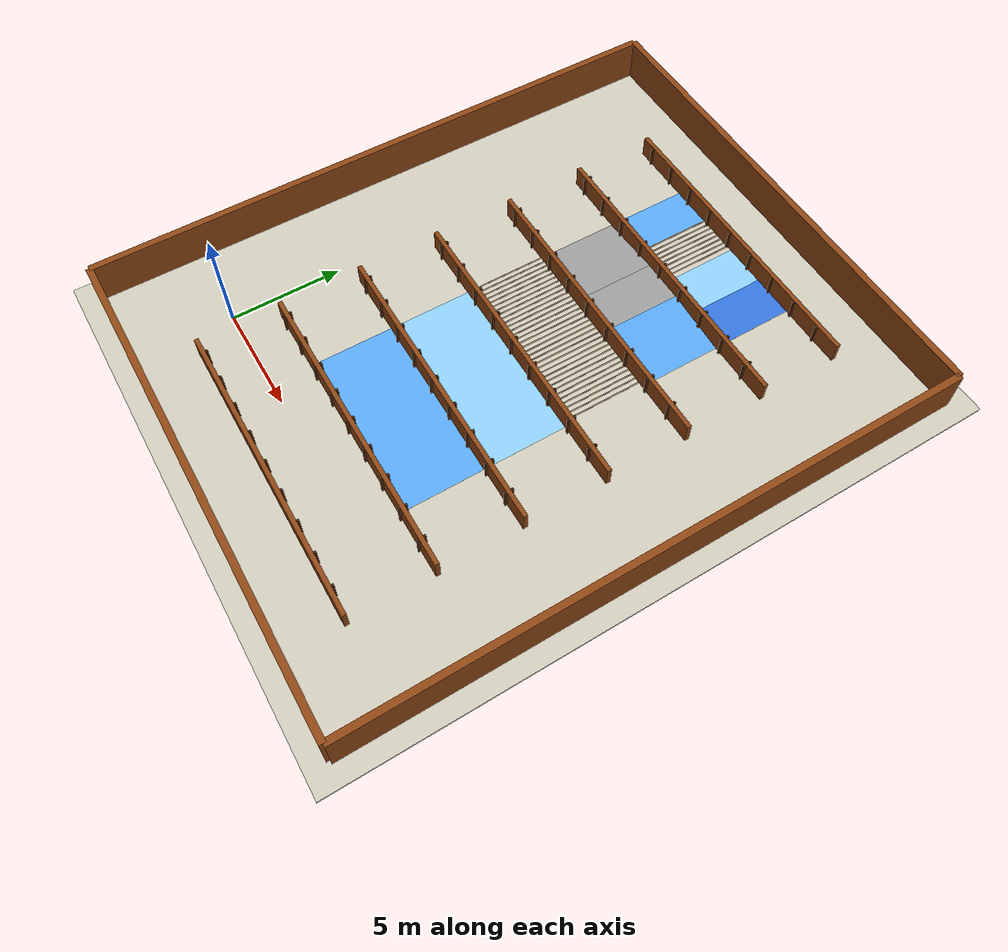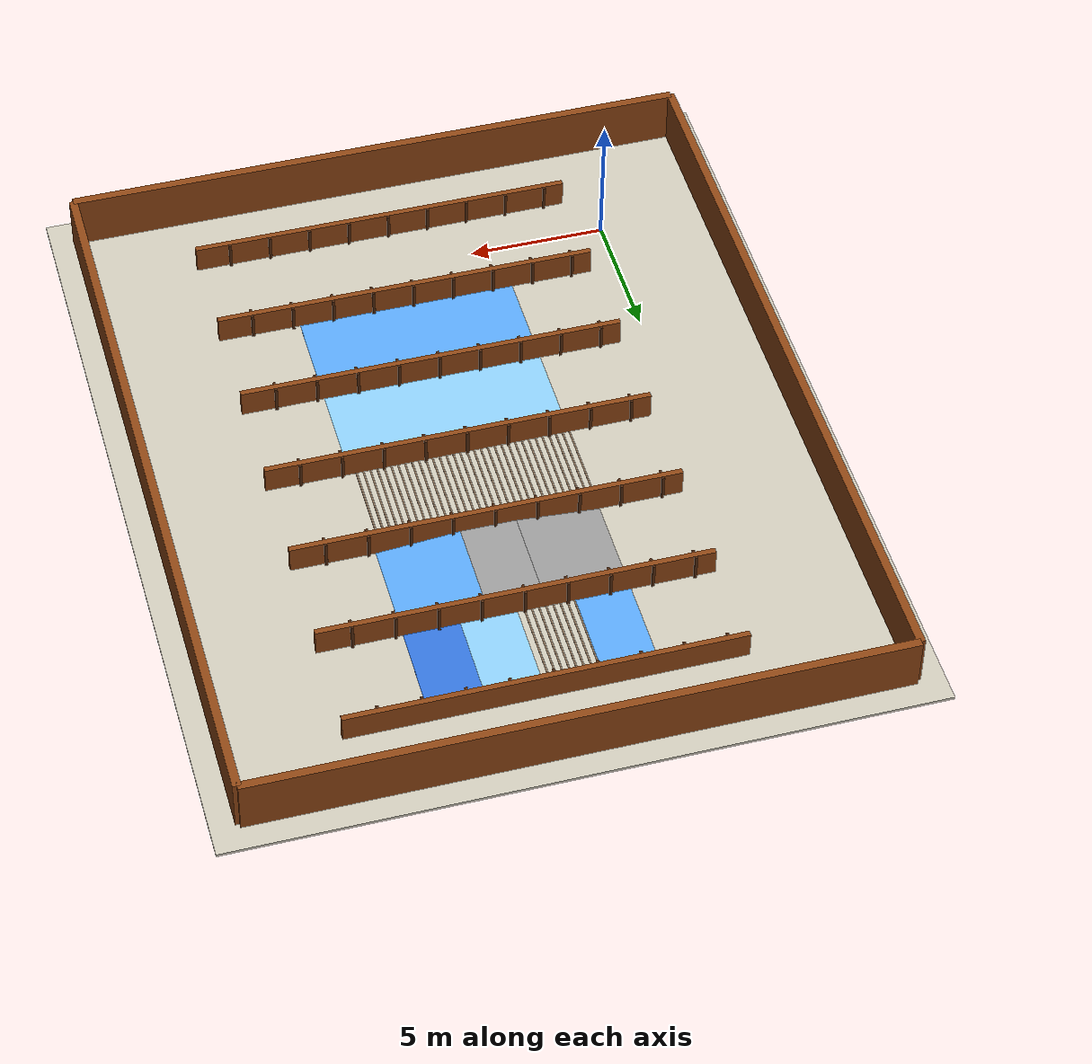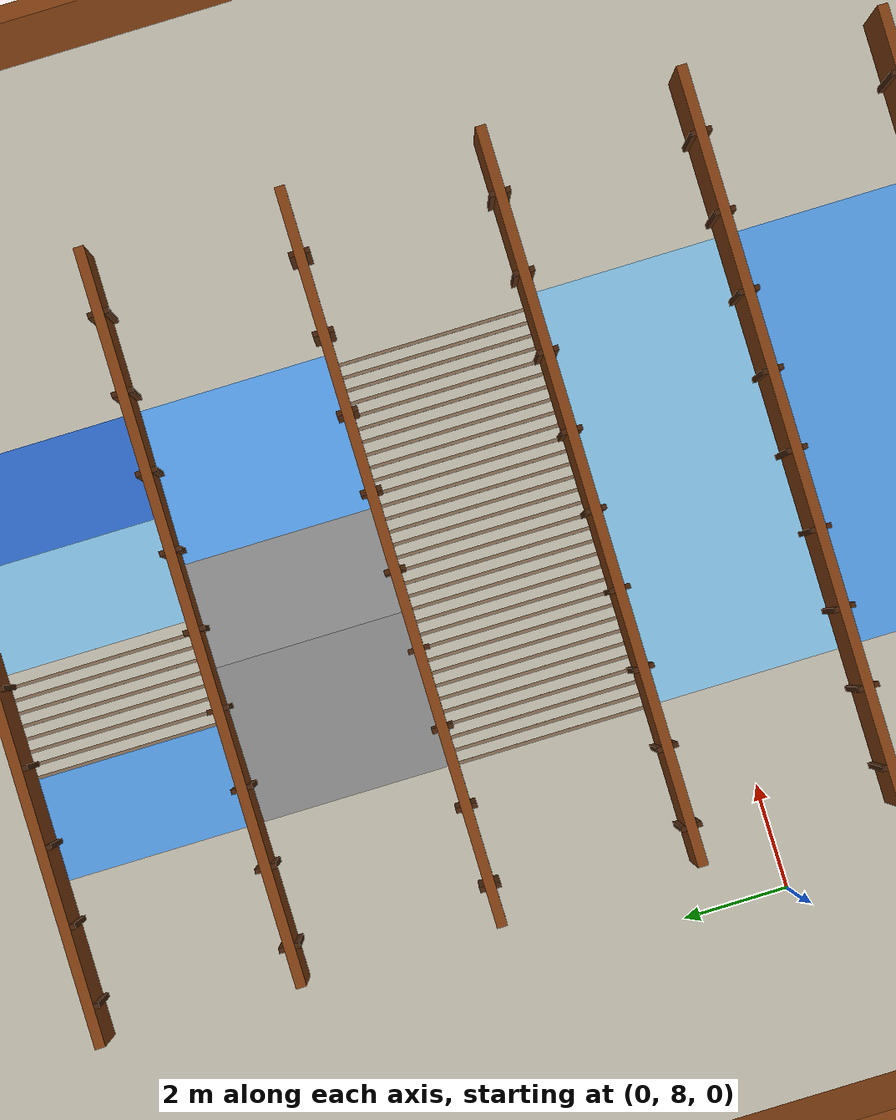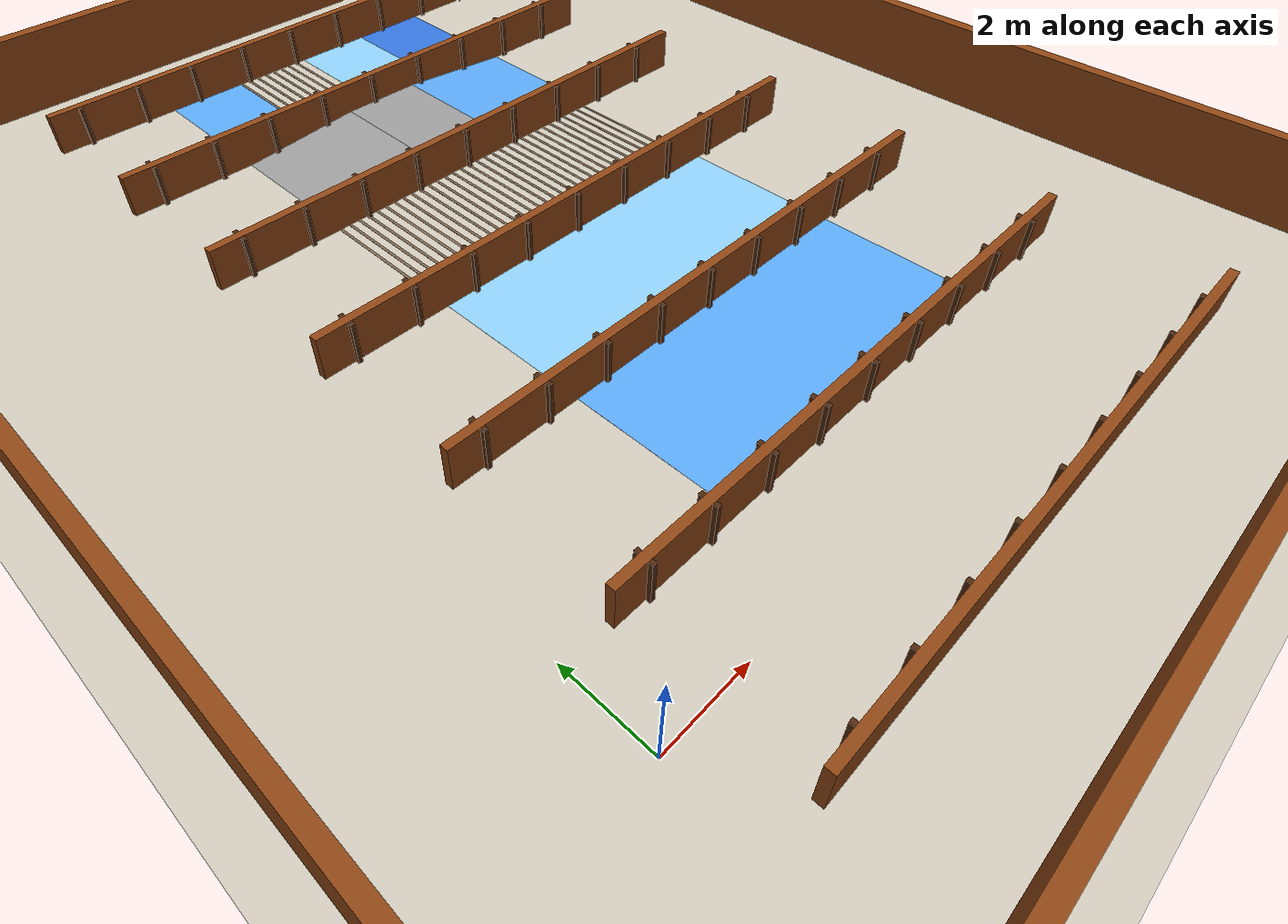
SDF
<?xml version="1.0" ?>
<!-- GENERATED by tools/gen_terrain_world.py — edit the generator, not this file. -->
<sdf version="1.6">
  <world name="terrain_world">
    <plugin filename="gz-sim-physics-system" name="gz::sim::systems::Physics"/>
    <plugin filename="gz-sim-scene-broadcaster-system" name="gz::sim::systems::SceneBroadcaster"/>
    <plugin filename="gz-sim-user-commands-system" name="gz::sim::systems::UserCommands"/>
    <light type="directional" name="sun">
      <cast_shadows>true</cast_shadows>
      <pose>0 0 10 0 0 0</pose>
      <diffuse>0.9 0.9 0.9 1</diffuse>
      <specular>0.3 0.3 0.3 1</specular>
      <direction>-0.5 0.1 -0.9</direction>
    </light>

    <model name="floor">
      <static>true</static>
      <pose>7.500 9.500 -0.05 0 0 0</pose>
      <link name="floor_link">
        <collision name="floor_collision"><geometry><box><size>25.0 30.0 0.1</size></box></geometry></collision>
        <visual name="floor_visual"><geometry><box><size>25.0 30.0 0.1</size></box></geometry>
          <material><ambient>0.80 0.78 0.72 1</ambient><diffuse>0.80 0.78 0.72 1</diffuse></material></visual>
      </link>
    </model>

    <model name="lane_wall_0">
      <static>true</static>
      <pose>8.0000 -1.9000 0.5000 0.00000 0.00000 0.00000</pose>
      <link name="link">
        <collision name="col">
          <geometry><box><size>14.0000 0.2000 1.0000</size></box></geometry>

        </collision>
        <visual name="vis">
          <geometry><box><size>14.0000 0.2000 1.0000</size></box></geometry>
          <material><ambient>0.55 0.27 0.08 1</ambient><diffuse>0.55 0.27 0.08 1</diffuse></material>
        </visual>
      </link>
    </model>
    <model name="lane_wall_1">
      <static>true</static>
      <pose>8.0000 1.9000 0.5000 0.00000 0.00000 0.00000</pose>
      <link name="link">
        <collision name="col">
          <geometry><box><size>14.0000 0.2000 1.0000</size></box></geometry>

        </collision>
        <visual name="vis">
          <geometry><box><size>14.0000 0.2000 1.0000</size></box></geometry>
          <material><ambient>0.55 0.27 0.08 1</ambient><diffuse>0.55 0.27 0.08 1</diffuse></material>
        </visual>
      </link>
    </model>
    <model name="lane_wall_2">
      <static>true</static>
      <pose>8.0000 5.7000 0.5000 0.00000 0.00000 0.00000</pose>
      <link name="link">
        <collision name="col">
          <geometry><box><size>14.0000 0.2000 1.0000</size></box></geometry>

        </collision>
        <visual name="vis">
          <geometry><box><size>14.0000 0.2000 1.0000</size></box></geometry>
          <material><ambient>0.55 0.27 0.08 1</ambient><diffuse>0.55 0.27 0.08 1</diffuse></material>
        </visual>
      </link>
    </model>
    <model name="lane_wall_3">
      <static>true</static>
      <pose>8.0000 9.5000 0.5000 0.00000 0.00000 0.00000</pose>
      <link name="link">
        <collision name="col">
          <geometry><box><size>14.0000 0.2000 1.0000</size></box></geometry>

        </collision>
        <visual name="vis">
          <geometry><box><size>14.0000 0.2000 1.0000</size></box></geometry>
          <material><ambient>0.55 0.27 0.08 1</ambient><diffuse>0.55 0.27 0.08 1</diffuse></material>
        </visual>
      </link>
    </model>
    <model name="lane_wall_4">
      <static>true</static>
      <pose>8.0000 13.3000 0.5000 0.00000 0.00000 0.00000</pose>
      <link name="link">
        <collision name="col">
          <geometry><box><size>14.0000 0.2000 1.0000</size></box></geometry>

        </collision>
        <visual name="vis">
          <geometry><box><size>14.0000 0.2000 1.0000</size></box></geometry>
          <material><ambient>0.55 0.27 0.08 1</ambient><diffuse>0.55 0.27 0.08 1</diffuse></material>
        </visual>
      </link>
    </model>
    <model name="lane_wall_5">
      <static>true</static>
      <pose>8.0000 17.1000 0.5000 0.00000 0.00000 0.00000</pose>
      <link name="link">
        <collision name="col">
          <geometry><box><size>14.0000 0.2000 1.0000</size></box></geometry>

        </collision>
        <visual name="vis">
          <geometry><box><size>14.0000 0.2000 1.0000</size></box></geometry>
          <material><ambient>0.55 0.27 0.08 1</ambient><diffuse>0.55 0.27 0.08 1</diffuse></material>
        </visual>
      </link>
    </model>
    <model name="lane_wall_6">
      <static>true</static>
      <pose>8.0000 20.9000 0.5000 0.00000 0.00000 0.00000</pose>
      <link name="link">
        <collision name="col">
          <geometry><box><size>14.0000 0.2000 1.0000</size></box></geometry>

        </collision>
        <visual name="vis">
          <geometry><box><size>14.0000 0.2000 1.0000</size></box></geometry>
          <material><ambient>0.55 0.27 0.08 1</ambient><diffuse>0.55 0.27 0.08 1</diffuse></material>
        </visual>
      </link>
    </model>
    <model name="lane0_rib_l0">
      <static>true</static>
      <pose>1.7500 1.7500 0.5000 0.00000 0.00000 0.00000</pose>
      <link name="link">
        <collision name="col">
          <geometry><box><size>0.1000 0.1000 1.0000</size></box></geometry>

        </collision>
        <visual name="vis">
          <geometry><box><size>0.1000 0.1000 1.0000</size></box></geometry>
          <material><ambient>0.30 0.15 0.05 1</ambient><diffuse>0.30 0.15 0.05 1</diffuse></material>
        </visual>
      </link>
    </model>
    <model name="lane0_rib_l1">
      <static>true</static>
      <pose>3.2500 1.7500 0.5000 0.00000 0.00000 0.00000</pose>
      <link name="link">
        <collision name="col">
          <geometry><box><size>0.1000 0.1000 1.0000</size></box></geometry>

        </collision>
        <visual name="vis">
          <geometry><box><size>0.1000 0.1000 1.0000</size></box></geometry>
          <material><ambient>0.30 0.15 0.05 1</ambient><diffuse>0.30 0.15 0.05 1</diffuse></material>
        </visual>
      </link>
    </model>
    <model name="lane0_rib_l2">
      <static>true</static>
      <pose>4.7500 1.7500 0.5000 0.00000 0.00000 0.00000</pose>
      <link name="link">
        <collision name="col">
          <geometry><box><size>0.1000 0.1000 1.0000</size></box></geometry>

        </collision>
        <visual name="vis">
          <geometry><box><size>0.1000 0.1000 1.0000</size></box></geometry>
          <material><ambient>0.30 0.15 0.05 1</ambient><diffuse>0.30 0.15 0.05 1</diffuse></material>
        </visual>
      </link>
    </model>
    <model name="lane0_rib_l3">
      <static>true</static>
      <pose>6.2500 1.7500 0.5000 0.00000 0.00000 0.00000</pose>
      <link name="link">
        <collision name="col">
          <geometry><box><size>0.1000 0.1000 1.0000</size></box></geometry>

        </collision>
        <visual name="vis">
          <geometry><box><size>0.1000 0.1000 1.0000</size></box></geometry>
          <material><ambient>0.30 0.15 0.05 1</ambient><diffuse>0.30 0.15 0.05 1</diffuse></material>
        </visual>
      </link>
    </model>
    <model name="lane0_rib_l4">
      <static>true</static>
      <pose>7.7500 1.7500 0.5000 0.00000 0.00000 0.00000</pose>
      <link name="link">
        <collision name="col">
          <geometry><box><size>0.1000 0.1000 1.0000</size></box></geometry>

        </collision>
        <visual name="vis">
          <geometry><box><size>0.1000 0.1000 1.0000</size></box></geometry>
          <material><ambient>0.30 0.15 0.05 1</ambient><diffuse>0.30 0.15 0.05 1</diffuse></material>
        </visual>
      </link>
    </model>
    <model name="lane0_rib_l5">
      <static>true</static>
      <pose>9.2500 1.7500 0.5000 0.00000 0.00000 0.00000</pose>
      <link name="link">
        <collision name="col">
          <geometry><box><size>0.1000 0.1000 1.0000</size></box></geometry>

        </collision>
        <visual name="vis">
          <geometry><box><size>0.1000 0.1000 1.0000</size></box></geometry>
          <material><ambient>0.30 0.15 0.05 1</ambient><diffuse>0.30 0.15 0.05 1</diffuse></material>
        </visual>
      </link>
    </model>
    <model name="lane0_rib_l6">
      <static>true</static>
      <pose>10.7500 1.7500 0.5000 0.00000 0.00000 0.00000</pose>
      <link name="link">
        <collision name="col">
          <geometry><box><size>0.1000 0.1000 1.0000</size></box></geometry>

        </collision>
        <visual name="vis">
          <geometry><box><size>0.1000 0.1000 1.0000</size></box></geometry>
          <material><ambient>0.30 0.15 0.05 1</ambient><diffuse>0.30 0.15 0.05 1</diffuse></material>
        </visual>
      </link>
    </model>
    <model name="lane0_rib_l7">
      <static>true</static>
      <pose>12.2500 1.7500 0.5000 0.00000 0.00000 0.00000</pose>
      <link name="link">
        <collision name="col">
          <geometry><box><size>0.1000 0.1000 1.0000</size></box></geometry>

        </collision>
        <visual name="vis">
          <geometry><box><size>0.1000 0.1000 1.0000</size></box></geometry>
          <material><ambient>0.30 0.15 0.05 1</ambient><diffuse>0.30 0.15 0.05 1</diffuse></material>
        </visual>
      </link>
    </model>
    <model name="lane0_rib_l8">
      <static>true</static>
      <pose>13.7500 1.7500 0.5000 0.00000 0.00000 0.00000</pose>
      <link name="link">
        <collision name="col">
          <geometry><box><size>0.1000 0.1000 1.0000</size></box></geometry>

        </collision>
        <visual name="vis">
          <geometry><box><size>0.1000 0.1000 1.0000</size></box></geometry>
          <material><ambient>0.30 0.15 0.05 1</ambient><diffuse>0.30 0.15 0.05 1</diffuse></material>
        </visual>
      </link>
    </model>
    <model name="lane0_rib_r0">
      <static>true</static>
      <pose>1.7500 -1.7500 0.5000 0.00000 0.00000 0.00000</pose>
      <link name="link">
        <collision name="col">
          <geometry><box><size>0.1000 0.1000 1.0000</size></box></geometry>

        </collision>
        <visual name="vis">
          <geometry><box><size>0.1000 0.1000 1.0000</size></box></geometry>
          <material><ambient>0.30 0.15 0.05 1</ambient><diffuse>0.30 0.15 0.05 1</diffuse></material>
        </visual>
      </link>
    </model>
    <model name="lane0_rib_r1">
      <static>true</static>
      <pose>3.2500 -1.7500 0.5000 0.00000 0.00000 0.00000</pose>
      <link name="link">
        <collision name="col">
          <geometry><box><size>0.1000 0.1000 1.0000</size></box></geometry>

        </collision>
        <visual name="vis">
          <geometry><box><size>0.1000 0.1000 1.0000</size></box></geometry>
          <material><ambient>0.30 0.15 0.05 1</ambient><diffuse>0.30 0.15 0.05 1</diffuse></material>
        </visual>
      </link>
    </model>
    <model name="lane0_rib_r2">
      <static>true</static>
      <pose>4.7500 -1.7500 0.5000 0.00000 0.00000 0.00000</pose>
      <link name="link">
        <collision name="col">
          <geometry><box><size>0.1000 0.1000 1.0000</size></box></geometry>

        </collision>
        <visual name="vis">
          <geometry><box><size>0.1000 0.1000 1.0000</size></box></geometry>
          <material><ambient>0.30 0.15 0.05 1</ambient><diffuse>0.30 0.15 0.05 1</diffuse></material>
        </visual>
      </link>
    </model>
    <model name="lane0_rib_r3">
      <static>true</static>
      <pose>6.2500 -1.7500 0.5000 0.00000 0.00000 0.00000</pose>
      <link name="link">
        <collision name="col">
          <geometry><box><size>0.1000 0.1000 1.0000</size></box></geometry>

        </collision>
        <visual name="vis">
          <geometry><box><size>0.1000 0.1000 1.0000</size></box></geometry>
          <material><ambient>0.30 0.15 0.05 1</ambient><diffuse>0.30 0.15 0.05 1</diffuse></material>
        </visual>
      </link>
    </model>
    <model name="lane0_rib_r4">
      <static>true</static>
      <pose>7.7500 -1.7500 0.5000 0.00000 0.00000 0.00000</pose>
      <link name="link">
        <collision name="col">
          <geometry><box><size>0.1000 0.1000 1.0000</size></box></geometry>

        </collision>
        <visual name="vis">
          <geometry><box><size>0.1000 0.1000 1.0000</size></box></geometry>
          <material><ambient>0.30 0.15 0.05 1</ambient><diffuse>0.30 0.15 0.05 1</diffuse></material>
        </visual>
      </link>
    </model>
    <model name="lane0_rib_r5">
      <static>true</static>
      <pose>9.2500 -1.7500 0.5000 0.00000 0.00000 0.00000</pose>
      <link name="link">
        <collision name="col">
          <geometry><box><size>0.1000 0.1000 1.0000</size></box></geometry>

        </collision>
        <visual name="vis">
          <geometry><box><size>0.1000 0.1000 1.0000</size></box></geometry>
          <material><ambient>0.30 0.15 0.05 1</ambient><diffuse>0.30 0.15 0.05 1</diffuse></material>
        </visual>
      </link>
    </model>
    <model name="lane0_rib_r6">
      <static>true</static>
      <pose>10.7500 -1.7500 0.5000 0.00000 0.00000 0.00000</pose>
      <link name="link">
        <collision name="col">
          <geometry><box><size>0.1000 0.1000 1.0000</size></box></geometry>

        </collision>
        <visual name="vis">
          <geometry><box><size>0.1000 0.1000 1.0000</size></box></geometry>
          <material><ambient>0.30 0.15 0.05 1</ambient><diffuse>0.30 0.15 0.05 1</diffuse></material>
        </visual>
      </link>
    </model>
    <model name="lane0_rib_r7">
      <static>true</static>
      <pose>12.2500 -1.7500 0.5000 0.00000 0.00000 0.00000</pose>
      <link name="link">
        <collision name="col">
          <geometry><box><size>0.1000 0.1000 1.0000</size></box></geometry>

        </collision>
        <visual name="vis">
          <geometry><box><size>0.1000 0.1000 1.0000</size></box></geometry>
          <material><ambient>0.30 0.15 0.05 1</ambient><diffuse>0.30 0.15 0.05 1</diffuse></material>
        </visual>
      </link>
    </model>
    <model name="lane0_rib_r8">
      <static>true</static>
      <pose>13.7500 -1.7500 0.5000 0.00000 0.00000 0.00000</pose>
      <link name="link">
        <collision name="col">
          <geometry><box><size>0.1000 0.1000 1.0000</size></box></geometry>

        </collision>
        <visual name="vis">
          <geometry><box><size>0.1000 0.1000 1.0000</size></box></geometry>
          <material><ambient>0.30 0.15 0.05 1</ambient><diffuse>0.30 0.15 0.05 1</diffuse></material>
        </visual>
      </link>
    </model>
    <model name="lane1_rib_l0">
      <static>true</static>
      <pose>1.7500 5.5500 0.5000 0.00000 0.00000 0.00000</pose>
      <link name="link">
        <collision name="col">
          <geometry><box><size>0.1000 0.1000 1.0000</size></box></geometry>

        </collision>
        <visual name="vis">
          <geometry><box><size>0.1000 0.1000 1.0000</size></box></geometry>
          <material><ambient>0.30 0.15 0.05 1</ambient><diffuse>0.30 0.15 0.05 1</diffuse></material>
        </visual>
      </link>
    </model>
    <model name="lane1_rib_l1">
      <static>true</static>
      <pose>3.2500 5.5500 0.5000 0.00000 0.00000 0.00000</pose>
      <link name="link">
        <collision name="col">
          <geometry><box><size>0.1000 0.1000 1.0000</size></box></geometry>

        </collision>
        <visual name="vis">
          <geometry><box><size>0.1000 0.1000 1.0000</size></box></geometry>
          <material><ambient>0.30 0.15 0.05 1</ambient><diffuse>0.30 0.15 0.05 1</diffuse></material>
        </visual>
      </link>
    </model>
    <model name="lane1_rib_l2">
      <static>true</static>
      <pose>4.7500 5.5500 0.5000 0.00000 0.00000 0.00000</pose>
      <link name="link">
        <collision name="col">
          <geometry><box><size>0.1000 0.1000 1.0000</size></box></geometry>

        </collision>
        <visual name="vis">
          <geometry><box><size>0.1000 0.1000 1.0000</size></box></geometry>
          <material><ambient>0.30 0.15 0.05 1</ambient><diffuse>0.30 0.15 0.05 1</diffuse></material>
        </visual>
      </link>
    </model>
    <model name="lane1_rib_l3">
      <static>true</static>
      <pose>6.2500 5.5500 0.5000 0.00000 0.00000 0.00000</pose>
      <link name="link">
        <collision name="col">
          <geometry><box><size>0.1000 0.1000 1.0000</size></box></geometry>

        </collision>
        <visual name="vis">
          <geometry><box><size>0.1000 0.1000 1.0000</size></box></geometry>
          <material><ambient>0.30 0.15 0.05 1</ambient><diffuse>0.30 0.15 0.05 1</diffuse></material>
        </visual>
      </link>
    </model>
    <model name="lane1_rib_l4">
      <static>true</static>
      <pose>7.7500 5.5500 0.5000 0.00000 0.00000 0.00000</pose>
      <link name="link">
        <collision name="col">
          <geometry><box><size>0.1000 0.1000 1.0000</size></box></geometry>

        </collision>
        <visual name="vis">
          <geometry><box><size>0.1000 0.1000 1.0000</size></box></geometry>
          <material><ambient>0.30 0.15 0.05 1</ambient><diffuse>0.30 0.15 0.05 1</diffuse></material>
        </visual>
      </link>
    </model>
    <model name="lane1_rib_l5">
      <static>true</static>
      <pose>9.2500 5.5500 0.5000 0.00000 0.00000 0.00000</pose>
      <link name="link">
        <collision name="col">
          <geometry><box><size>0.1000 0.1000 1.0000</size></box></geometry>

        </collision>
        <visual name="vis">
          <geometry><box><size>0.1000 0.1000 1.0000</size></box></geometry>
          <material><ambient>0.30 0.15 0.05 1</ambient><diffuse>0.30 0.15 0.05 1</diffuse></material>
        </visual>
      </link>
    </model>
    <model name="lane1_rib_l6">
      <static>true</static>
      <pose>10.7500 5.5500 0.5000 0.00000 0.00000 0.00000</pose>
      <link name="link">
        <collision name="col">
          <geometry><box><size>0.1000 0.1000 1.0000</size></box></geometry>

        </collision>
        <visual name="vis">
          <geometry><box><size>0.1000 0.1000 1.0000</size></box></geometry>
          <material><ambient>0.30 0.15 0.05 1</ambient><diffuse>0.30 0.15 0.05 1</diffuse></material>
        </visual>
      </link>
    </model>
    <model name="lane1_rib_l7">
      <static>true</static>
      <pose>12.2500 5.5500 0.5000 0.00000 0.00000 0.00000</pose>
      <link name="link">
        <collision name="col">
          <geometry><box><size>0.1000 0.1000 1.0000</size></box></geometry>

        </collision>
        <visual name="vis">
          <geometry><box><size>0.1000 0.1000 1.0000</size></box></geometry>
          <material><ambient>0.30 0.15 0.05 1</ambient><diffuse>0.30 0.15 0.05 1</diffuse></material>
        </visual>
      </link>
    </model>
    <model name="lane1_rib_l8">
      <static>true</static>
      <pose>13.7500 5.5500 0.5000 0.00000 0.00000 0.00000</pose>
      <link name="link">
        <collision name="col">
          <geometry><box><size>0.1000 0.1000 1.0000</size></box></geometry>

        </collision>
        <visual name="vis">
          <geometry><box><size>0.1000 0.1000 1.0000</size></box></geometry>
          <material><ambient>0.30 0.15 0.05 1</ambient><diffuse>0.30 0.15 0.05 1</diffuse></material>
        </visual>
      </link>
    </model>
    <model name="lane1_rib_r0">
      <static>true</static>
      <pose>1.7500 2.0500 0.5000 0.00000 0.00000 0.00000</pose>
      <link name="link">
        <collision name="col">
          <geometry><box><size>0.1000 0.1000 1.0000</size></box></geometry>

        </collision>
        <visual name="vis">
          <geometry><box><size>0.1000 0.1000 1.0000</size></box></geometry>
          <material><ambient>0.30 0.15 0.05 1</ambient><diffuse>0.30 0.15 0.05 1</diffuse></material>
        </visual>
      </link>
    </model>
    <model name="lane1_rib_r1">
      <static>true</static>
      <pose>3.2500 2.0500 0.5000 0.00000 0.00000 0.00000</pose>
      <link name="link">
        <collision name="col">
          <geometry><box><size>0.1000 0.1000 1.0000</size></box></geometry>

        </collision>
        <visual name="vis">
          <geometry><box><size>0.1000 0.1000 1.0000</size></box></geometry>
          <material><ambient>0.30 0.15 0.05 1</ambient><diffuse>0.30 0.15 0.05 1</diffuse></material>
        </visual>
      </link>
    </model>
    <model name="lane1_rib_r2">
      <static>true</static>
      <pose>4.7500 2.0500 0.5000 0.00000 0.00000 0.00000</pose>
      <link name="link">
        <collision name="col">
          <geometry><box><size>0.1000 0.1000 1.0000</size></box></geometry>

        </collision>
        <visual name="vis">
          <geometry><box><size>0.1000 0.1000 1.0000</size></box></geometry>
          <material><ambient>0.30 0.15 0.05 1</ambient><diffuse>0.30 0.15 0.05 1</diffuse></material>
        </visual>
      </link>
    </model>
    <model name="lane1_rib_r3">
      <static>true</static>
      <pose>6.2500 2.0500 0.5000 0.00000 0.00000 0.00000</pose>
      <link name="link">
        <collision name="col">
          <geometry><box><size>0.1000 0.1000 1.0000</size></box></geometry>

        </collision>
        <visual name="vis">
          <geometry><box><size>0.1000 0.1000 1.0000</size></box></geometry>
          <material><ambient>0.30 0.15 0.05 1</ambient><diffuse>0.30 0.15 0.05 1</diffuse></material>
        </visual>
      </link>
    </model>
    <model name="lane1_rib_r4">
      <static>true</static>
      <pose>7.7500 2.0500 0.5000 0.00000 0.00000 0.00000</pose>
      <link name="link">
        <collision name="col">
          <geometry><box><size>0.1000 0.1000 1.0000</size></box></geometry>

        </collision>
        <visual name="vis">
          <geometry><box><size>0.1000 0.1000 1.0000</size></box></geometry>
          <material><ambient>0.30 0.15 0.05 1</ambient><diffuse>0.30 0.15 0.05 1</diffuse></material>
        </visual>
      </link>
    </model>
    <model name="lane1_rib_r5">
      <static>true</static>
      <pose>9.2500 2.0500 0.5000 0.00000 0.00000 0.00000</pose>
      <link name="link">
        <collision name="col">
          <geometry><box><size>0.1000 0.1000 1.0000</size></box></geometry>

        </collision>
        <visual name="vis">
          <geometry><box><size>0.1000 0.1000 1.0000</size></box></geometry>
          <material><ambient>0.30 0.15 0.05 1</ambient><diffuse>0.30 0.15 0.05 1</diffuse></material>
        </visual>
      </link>
    </model>
    <model name="lane1_rib_r6">
      <static>true</static>
      <pose>10.7500 2.0500 0.5000 0.00000 0.00000 0.00000</pose>
      <link name="link">
        <collision name="col">
          <geometry><box><size>0.1000 0.1000 1.0000</size></box></geometry>

        </collision>
        <visual name="vis">
          <geometry><box><size>0.1000 0.1000 1.0000</size></box></geometry>
          <material><ambient>0.30 0.15 0.05 1</ambient><diffuse>0.30 0.15 0.05 1</diffuse></material>
        </visual>
      </link>
    </model>
    <model name="lane1_rib_r7">
      <static>true</static>
      <pose>12.2500 2.0500 0.5000 0.00000 0.00000 0.00000</pose>
      <link name="link">
        <collision name="col">
          <geometry><box><size>0.1000 0.1000 1.0000</size></box></geometry>

        </collision>
        <visual name="vis">
          <geometry><box><size>0.1000 0.1000 1.0000</size></box></geometry>
          <material><ambient>0.30 0.15 0.05 1</ambient><diffuse>0.30 0.15 0.05 1</diffuse></material>
        </visual>
      </link>
    </model>
    <model name="lane1_rib_r8">
      <static>true</static>
      <pose>13.7500 2.0500 0.5000 0.00000 0.00000 0.00000</pose>
      <link name="link">
        <collision name="col">
          <geometry><box><size>0.1000 0.1000 1.0000</size></box></geometry>

        </collision>
        <visual name="vis">
          <geometry><box><size>0.1000 0.1000 1.0000</size></box></geometry>
          <material><ambient>0.30 0.15 0.05 1</ambient><diffuse>0.30 0.15 0.05 1</diffuse></material>
        </visual>
      </link>
    </model>
    <model name="lane2_rib_l0">
      <static>true</static>
      <pose>1.7500 9.3500 0.5000 0.00000 0.00000 0.00000</pose>
      <link name="link">
        <collision name="col">
          <geometry><box><size>0.1000 0.1000 1.0000</size></box></geometry>

        </collision>
        <visual name="vis">
          <geometry><box><size>0.1000 0.1000 1.0000</size></box></geometry>
          <material><ambient>0.30 0.15 0.05 1</ambient><diffuse>0.30 0.15 0.05 1</diffuse></material>
        </visual>
      </link>
    </model>
    <model name="lane2_rib_l1">
      <static>true</static>
      <pose>3.2500 9.3500 0.5000 0.00000 0.00000 0.00000</pose>
      <link name="link">
        <collision name="col">
          <geometry><box><size>0.1000 0.1000 1.0000</size></box></geometry>

        </collision>
        <visual name="vis">
          <geometry><box><size>0.1000 0.1000 1.0000</size></box></geometry>
          <material><ambient>0.30 0.15 0.05 1</ambient><diffuse>0.30 0.15 0.05 1</diffuse></material>
        </visual>
      </link>
    </model>
    <model name="lane2_rib_l2">
      <static>true</static>
      <pose>4.7500 9.3500 0.5000 0.00000 0.00000 0.00000</pose>
      <link name="link">
        <collision name="col">
          <geometry><box><size>0.1000 0.1000 1.0000</size></box></geometry>

        </collision>
        <visual name="vis">
          <geometry><box><size>0.1000 0.1000 1.0000</size></box></geometry>
          <material><ambient>0.30 0.15 0.05 1</ambient><diffuse>0.30 0.15 0.05 1</diffuse></material>
        </visual>
      </link>
    </model>
    <model name="lane2_rib_l3">
      <static>true</static>
      <pose>6.2500 9.3500 0.5000 0.00000 0.00000 0.00000</pose>
      <link name="link">
        <collision name="col">
          <geometry><box><size>0.1000 0.1000 1.0000</size></box></geometry>

        </collision>
        <visual name="vis">
          <geometry><box><size>0.1000 0.1000 1.0000</size></box></geometry>
          <material><ambient>0.30 0.15 0.05 1</ambient><diffuse>0.30 0.15 0.05 1</diffuse></material>
        </visual>
      </link>
    </model>
    <model name="lane2_rib_l4">
      <static>true</static>
      <pose>7.7500 9.3500 0.5000 0.00000 0.00000 0.00000</pose>
      <link name="link">
        <collision name="col">
          <geometry><box><size>0.1000 0.1000 1.0000</size></box></geometry>

        </collision>
        <visual name="vis">
          <geometry><box><size>0.1000 0.1000 1.0000</size></box></geometry>
          <material><ambient>0.30 0.15 0.05 1</ambient><diffuse>0.30 0.15 0.05 1</diffuse></material>
        </visual>
      </link>
    </model>
    <model name="lane2_rib_l5">
      <static>true</static>
      <pose>9.2500 9.3500 0.5000 0.00000 0.00000 0.00000</pose>
      <link name="link">
        <collision name="col">
          <geometry><box><size>0.1000 0.1000 1.0000</size></box></geometry>

        </collision>
        <visual name="vis">
          <geometry><box><size>0.1000 0.1000 1.0000</size></box></geometry>
          <material><ambient>0.30 0.15 0.05 1</ambient><diffuse>0.30 0.15 0.05 1</diffuse></material>
        </visual>
      </link>
    </model>
    <model name="lane2_rib_l6">
      <static>true</static>
      <pose>10.7500 9.3500 0.5000 0.00000 0.00000 0.00000</pose>
      <link name="link">
        <collision name="col">
          <geometry><box><size>0.1000 0.1000 1.0000</size></box></geometry>

        </collision>
        <visual name="vis">
          <geometry><box><size>0.1000 0.1000 1.0000</size></box></geometry>
          <material><ambient>0.30 0.15 0.05 1</ambient><diffuse>0.30 0.15 0.05 1</diffuse></material>
        </visual>
      </link>
    </model>
    <model name="lane2_rib_l7">
      <static>true</static>
      <pose>12.2500 9.3500 0.5000 0.00000 0.00000 0.00000</pose>
      <link name="link">
        <collision name="col">
          <geometry><box><size>0.1000 0.1000 1.0000</size></box></geometry>

        </collision>
        <visual name="vis">
          <geometry><box><size>0.1000 0.1000 1.0000</size></box></geometry>
          <material><ambient>0.30 0.15 0.05 1</ambient><diffuse>0.30 0.15 0.05 1</diffuse></material>
        </visual>
      </link>
    </model>
    <model name="lane2_rib_l8">
      <static>true</static>
      <pose>13.7500 9.3500 0.5000 0.00000 0.00000 0.00000</pose>
      <link name="link">
        <collision name="col">
          <geometry><box><size>0.1000 0.1000 1.0000</size></box></geometry>

        </collision>
        <visual name="vis">
          <geometry><box><size>0.1000 0.1000 1.0000</size></box></geometry>
          <material><ambient>0.30 0.15 0.05 1</ambient><diffuse>0.30 0.15 0.05 1</diffuse></material>
        </visual>
      </link>
    </model>
    <model name="lane2_rib_r0">
      <static>true</static>
      <pose>1.7500 5.8500 0.5000 0.00000 0.00000 0.00000</pose>
      <link name="link">
        <collision name="col">
          <geometry><box><size>0.1000 0.1000 1.0000</size></box></geometry>

        </collision>
        <visual name="vis">
          <geometry><box><size>0.1000 0.1000 1.0000</size></box></geometry>
          <material><ambient>0.30 0.15 0.05 1</ambient><diffuse>0.30 0.15 0.05 1</diffuse></material>
        </visual>
      </link>
    </model>
    <model name="lane2_rib_r1">
      <static>true</static>
      <pose>3.2500 5.8500 0.5000 0.00000 0.00000 0.00000</pose>
      <link name="link">
        <collision name="col">
          <geometry><box><size>0.1000 0.1000 1.0000</size></box></geometry>

        </collision>
        <visual name="vis">
          <geometry><box><size>0.1000 0.1000 1.0000</size></box></geometry>
          <material><ambient>0.30 0.15 0.05 1</ambient><diffuse>0.30 0.15 0.05 1</diffuse></material>
        </visual>
      </link>
    </model>
    <model name="lane2_rib_r2">
      <static>true</static>
      <pose>4.7500 5.8500 0.5000 0.00000 0.00000 0.00000</pose>
      <link name="link">
        <collision name="col">
          <geometry><box><size>0.1000 0.1000 1.0000</size></box></geometry>

        </collision>
        <visual name="vis">
          <geometry><box><size>0.1000 0.1000 1.0000</size></box></geometry>
          <material><ambient>0.30 0.15 0.05 1</ambient><diffuse>0.30 0.15 0.05 1</diffuse></material>
        </visual>
      </link>
    </model>
    <model name="lane2_rib_r3">
      <static>true</static>
      <pose>6.2500 5.8500 0.5000 0.00000 0.00000 0.00000</pose>
      <link name="link">
        <collision name="col">
          <geometry><box><size>0.1000 0.1000 1.0000</size></box></geometry>

        </collision>
        <visual name="vis">
          <geometry><box><size>0.1000 0.1000 1.0000</size></box></geometry>
          <material><ambient>0.30 0.15 0.05 1</ambient><diffuse>0.30 0.15 0.05 1</diffuse></material>
        </visual>
      </link>
    </model>
    <model name="lane2_rib_r4">
      <static>true</static>
      <pose>7.7500 5.8500 0.5000 0.00000 0.00000 0.00000</pose>
      <link name="link">
        <collision name="col">
          <geometry><box><size>0.1000 0.1000 1.0000</size></box></geometry>

        </collision>
        <visual name="vis">
          <geometry><box><size>0.1000 0.1000 1.0000</size></box></geometry>
          <material><ambient>0.30 0.15 0.05 1</ambient><diffuse>0.30 0.15 0.05 1</diffuse></material>
        </visual>
      </link>
    </model>
    <model name="lane2_rib_r5">
      <static>true</static>
      <pose>9.2500 5.8500 0.5000 0.00000 0.00000 0.00000</pose>
      <link name="link">
        <collision name="col">
          <geometry><box><size>0.1000 0.1000 1.0000</size></box></geometry>

        </collision>
        <visual name="vis">
          <geometry><box><size>0.1000 0.1000 1.0000</size></box></geometry>
          <material><ambient>0.30 0.15 0.05 1</ambient><diffuse>0.30 0.15 0.05 1</diffuse></material>
        </visual>
      </link>
    </model>
    <model name="lane2_rib_r6">
      <static>true</static>
      <pose>10.7500 5.8500 0.5000 0.00000 0.00000 0.00000</pose>
      <link name="link">
        <collision name="col">
          <geometry><box><size>0.1000 0.1000 1.0000</size></box></geometry>

        </collision>
        <visual name="vis">
          <geometry><box><size>0.1000 0.1000 1.0000</size></box></geometry>
          <material><ambient>0.30 0.15 0.05 1</ambient><diffuse>0.30 0.15 0.05 1</diffuse></material>
        </visual>
      </link>
    </model>
    <model name="lane2_rib_r7">
      <static>true</static>
      <pose>12.2500 5.8500 0.5000 0.00000 0.00000 0.00000</pose>
      <link name="link">
        <collision name="col">
          <geometry><box><size>0.1000 0.1000 1.0000</size></box></geometry>

        </collision>
        <visual name="vis">
          <geometry><box><size>0.1000 0.1000 1.0000</size></box></geometry>
          <material><ambient>0.30 0.15 0.05 1</ambient><diffuse>0.30 0.15 0.05 1</diffuse></material>
        </visual>
      </link>
    </model>
    <model name="lane2_rib_r8">
      <static>true</static>
      <pose>13.7500 5.8500 0.5000 0.00000 0.00000 0.00000</pose>
      <link name="link">
        <collision name="col">
          <geometry><box><size>0.1000 0.1000 1.0000</size></box></geometry>

        </collision>
        <visual name="vis">
          <geometry><box><size>0.1000 0.1000 1.0000</size></box></geometry>
          <material><ambient>0.30 0.15 0.05 1</ambient><diffuse>0.30 0.15 0.05 1</diffuse></material>
        </visual>
      </link>
    </model>
    <model name="lane3_rib_l0">
      <static>true</static>
      <pose>1.7500 13.1500 0.5000 0.00000 0.00000 0.00000</pose>
      <link name="link">
        <collision name="col">
          <geometry><box><size>0.1000 0.1000 1.0000</size></box></geometry>

        </collision>
        <visual name="vis">
          <geometry><box><size>0.1000 0.1000 1.0000</size></box></geometry>
          <material><ambient>0.30 0.15 0.05 1</ambient><diffuse>0.30 0.15 0.05 1</diffuse></material>
        </visual>
      </link>
    </model>
    <model name="lane3_rib_l1">
      <static>true</static>
      <pose>3.2500 13.1500 0.5000 0.00000 0.00000 0.00000</pose>
      <link name="link">
        <collision name="col">
          <geometry><box><size>0.1000 0.1000 1.0000</size></box></geometry>

        </collision>
        <visual name="vis">
          <geometry><box><size>0.1000 0.1000 1.0000</size></box></geometry>
          <material><ambient>0.30 0.15 0.05 1</ambient><diffuse>0.30 0.15 0.05 1</diffuse></material>
        </visual>
      </link>
    </model>
    <model name="lane3_rib_l2">
      <static>true</static>
      <pose>4.7500 13.1500 0.5000 0.00000 0.00000 0.00000</pose>
      <link name="link">
        <collision name="col">
          <geometry><box><size>0.1000 0.1000 1.0000</size></box></geometry>

        </collision>
        <visual name="vis">
          <geometry><box><size>0.1000 0.1000 1.0000</size></box></geometry>
          <material><ambient>0.30 0.15 0.05 1</ambient><diffuse>0.30 0.15 0.05 1</diffuse></material>
        </visual>
      </link>
    </model>
    <model name="lane3_rib_l3">
      <static>true</static>
      <pose>6.2500 13.1500 0.5000 0.00000 0.00000 0.00000</pose>
      <link name="link">
        <collision name="col">
          <geometry><box><size>0.1000 0.1000 1.0000</size></box></geometry>

        </collision>
        <visual name="vis">
          <geometry><box><size>0.1000 0.1000 1.0000</size></box></geometry>
          <material><ambient>0.30 0.15 0.05 1</ambient><diffuse>0.30 0.15 0.05 1</diffuse></material>
        </visual>
      </link>
    </model>
    <model name="lane3_rib_l4">
      <static>true</static>
      <pose>7.7500 13.1500 0.5000 0.00000 0.00000 0.00000</pose>
      <link name="link">
        <collision name="col">
          <geometry><box><size>0.1000 0.1000 1.0000</size></box></geometry>

        </collision>
        <visual name="vis">
          <geometry><box><size>0.1000 0.1000 1.0000</size></box></geometry>
          <material><ambient>0.30 0.15 0.05 1</ambient><diffuse>0.30 0.15 0.05 1</diffuse></material>
        </visual>
      </link>
    </model>
    <model name="lane3_rib_l5">
      <static>true</static>
      <pose>9.2500 13.1500 0.5000 0.00000 0.00000 0.00000</pose>
      <link name="link">
        <collision name="col">
          <geometry><box><size>0.1000 0.1000 1.0000</size></box></geometry>

        </collision>
        <visual name="vis">
          <geometry><box><size>0.1000 0.1000 1.0000</size></box></geometry>
          <material><ambient>0.30 0.15 0.05 1</ambient><diffuse>0.30 0.15 0.05 1</diffuse></material>
        </visual>
      </link>
    </model>
    <model name="lane3_rib_l6">
      <static>true</static>
      <pose>10.7500 13.1500 0.5000 0.00000 0.00000 0.00000</pose>
      <link name="link">
        <collision name="col">
          <geometry><box><size>0.1000 0.1000 1.0000</size></box></geometry>

        </collision>
        <visual name="vis">
          <geometry><box><size>0.1000 0.1000 1.0000</size></box></geometry>
          <material><ambient>0.30 0.15 0.05 1</ambient><diffuse>0.30 0.15 0.05 1</diffuse></material>
        </visual>
      </link>
    </model>
    <model name="lane3_rib_l7">
      <static>true</static>
      <pose>12.2500 13.1500 0.5000 0.00000 0.00000 0.00000</pose>
      <link name="link">
        <collision name="col">
          <geometry><box><size>0.1000 0.1000 1.0000</size></box></geometry>

        </collision>
        <visual name="vis">
          <geometry><box><size>0.1000 0.1000 1.0000</size></box></geometry>
          <material><ambient>0.30 0.15 0.05 1</ambient><diffuse>0.30 0.15 0.05 1</diffuse></material>
        </visual>
      </link>
    </model>
    <model name="lane3_rib_l8">
      <static>true</static>
      <pose>13.7500 13.1500 0.5000 0.00000 0.00000 0.00000</pose>
      <link name="link">
        <collision name="col">
          <geometry><box><size>0.1000 0.1000 1.0000</size></box></geometry>

        </collision>
        <visual name="vis">
          <geometry><box><size>0.1000 0.1000 1.0000</size></box></geometry>
          <material><ambient>0.30 0.15 0.05 1</ambient><diffuse>0.30 0.15 0.05 1</diffuse></material>
        </visual>
      </link>
    </model>
    <model name="lane3_rib_r0">
      <static>true</static>
      <pose>1.7500 9.6500 0.5000 0.00000 0.00000 0.00000</pose>
      <link name="link">
        <collision name="col">
          <geometry><box><size>0.1000 0.1000 1.0000</size></box></geometry>

        </collision>
        <visual name="vis">
          <geometry><box><size>0.1000 0.1000 1.0000</size></box></geometry>
          <material><ambient>0.30 0.15 0.05 1</ambient><diffuse>0.30 0.15 0.05 1</diffuse></material>
        </visual>
      </link>
    </model>
    <model name="lane3_rib_r1">
      <static>true</static>
      <pose>3.2500 9.6500 0.5000 0.00000 0.00000 0.00000</pose>
      <link name="link">
        <collision name="col">
          <geometry><box><size>0.1000 0.1000 1.0000</size></box></geometry>

        </collision>
        <visual name="vis">
          <geometry><box><size>0.1000 0.1000 1.0000</size></box></geometry>
          <material><ambient>0.30 0.15 0.05 1</ambient><diffuse>0.30 0.15 0.05 1</diffuse></material>
        </visual>
      </link>
    </model>
    <model name="lane3_rib_r2">
      <static>true</static>
      <pose>4.7500 9.6500 0.5000 0.00000 0.00000 0.00000</pose>
      <link name="link">
        <collision name="col">
          <geometry><box><size>0.1000 0.1000 1.0000</size></box></geometry>

        </collision>
        <visual name="vis">
          <geometry><box><size>0.1000 0.1000 1.0000</size></box></geometry>
          <material><ambient>0.30 0.15 0.05 1</ambient><diffuse>0.30 0.15 0.05 1</diffuse></material>
        </visual>
      </link>
    </model>
    <model name="lane3_rib_r3">
      <static>true</static>
      <pose>6.2500 9.6500 0.5000 0.00000 0.00000 0.00000</pose>
      <link name="link">
        <collision name="col">
          <geometry><box><size>0.1000 0.1000 1.0000</size></box></geometry>

        </collision>
        <visual name="vis">
          <geometry><box><size>0.1000 0.1000 1.0000</size></box></geometry>
          <material><ambient>0.30 0.15 0.05 1</ambient><diffuse>0.30 0.15 0.05 1</diffuse></material>
        </visual>
      </link>
    </model>
    <model name="lane3_rib_r4">
      <static>true</static>
      <pose>7.7500 9.6500 0.5000 0.00000 0.00000 0.00000</pose>
      <link name="link">
        <collision name="col">
          <geometry><box><size>0.1000 0.1000 1.0000</size></box></geometry>

        </collision>
        <visual name="vis">
          <geometry><box><size>0.1000 0.1000 1.0000</size></box></geometry>
          <material><ambient>0.30 0.15 0.05 1</ambient><diffuse>0.30 0.15 0.05 1</diffuse></material>
        </visual>
      </link>
    </model>
    <model name="lane3_rib_r5">
      <static>true</static>
      <pose>9.2500 9.6500 0.5000 0.00000 0.00000 0.00000</pose>
      <link name="link">
        <collision name="col">
          <geometry><box><size>0.1000 0.1000 1.0000</size></box></geometry>

        </collision>
        <visual name="vis">
          <geometry><box><size>0.1000 0.1000 1.0000</size></box></geometry>
          <material><ambient>0.30 0.15 0.05 1</ambient><diffuse>0.30 0.15 0.05 1</diffuse></material>
        </visual>
      </link>
    </model>
    <model name="lane3_rib_r6">
      <static>true</static>
      <pose>10.7500 9.6500 0.5000 0.00000 0.00000 0.00000</pose>
      <link name="link">
        <collision name="col">
          <geometry><box><size>0.1000 0.1000 1.0000</size></box></geometry>

        </collision>
        <visual name="vis">
          <geometry><box><size>0.1000 0.1000 1.0000</size></box></geometry>
          <material><ambient>0.30 0.15 0.05 1</ambient><diffuse>0.30 0.15 0.05 1</diffuse></material>
        </visual>
      </link>
    </model>
    <model name="lane3_rib_r7">
      <static>true</static>
      <pose>12.2500 9.6500 0.5000 0.00000 0.00000 0.00000</pose>
      <link name="link">
        <collision name="col">
          <geometry><box><size>0.1000 0.1000 1.0000</size></box></geometry>

        </collision>
        <visual name="vis">
          <geometry><box><size>0.1000 0.1000 1.0000</size></box></geometry>
          <material><ambient>0.30 0.15 0.05 1</ambient><diffuse>0.30 0.15 0.05 1</diffuse></material>
        </visual>
      </link>
    </model>
    <model name="lane3_rib_r8">
      <static>true</static>
      <pose>13.7500 9.6500 0.5000 0.00000 0.00000 0.00000</pose>
      <link name="link">
        <collision name="col">
          <geometry><box><size>0.1000 0.1000 1.0000</size></box></geometry>

        </collision>
        <visual name="vis">
          <geometry><box><size>0.1000 0.1000 1.0000</size></box></geometry>
          <material><ambient>0.30 0.15 0.05 1</ambient><diffuse>0.30 0.15 0.05 1</diffuse></material>
        </visual>
      </link>
    </model>
    <model name="lane4_rib_l0">
      <static>true</static>
      <pose>1.7500 16.9500 0.5000 0.00000 0.00000 0.00000</pose>
      <link name="link">
        <collision name="col">
          <geometry><box><size>0.1000 0.1000 1.0000</size></box></geometry>

        </collision>
        <visual name="vis">
          <geometry><box><size>0.1000 0.1000 1.0000</size></box></geometry>
          <material><ambient>0.30 0.15 0.05 1</ambient><diffuse>0.30 0.15 0.05 1</diffuse></material>
        </visual>
      </link>
    </model>
    <model name="lane4_rib_l1">
      <static>true</static>
      <pose>3.2500 16.9500 0.5000 0.00000 0.00000 0.00000</pose>
      <link name="link">
        <collision name="col">
          <geometry><box><size>0.1000 0.1000 1.0000</size></box></geometry>

        </collision>
        <visual name="vis">
          <geometry><box><size>0.1000 0.1000 1.0000</size></box></geometry>
          <material><ambient>0.30 0.15 0.05 1</ambient><diffuse>0.30 0.15 0.05 1</diffuse></material>
        </visual>
      </link>
    </model>
    <model name="lane4_rib_l2">
      <static>true</static>
      <pose>4.7500 16.9500 0.5000 0.00000 0.00000 0.00000</pose>
      <link name="link">
        <collision name="col">
          <geometry><box><size>0.1000 0.1000 1.0000</size></box></geometry>

        </collision>
        <visual name="vis">
          <geometry><box><size>0.1000 0.1000 1.0000</size></box></geometry>
          <material><ambient>0.30 0.15 0.05 1</ambient><diffuse>0.30 0.15 0.05 1</diffuse></material>
        </visual>
      </link>
    </model>
    <model name="lane4_rib_l3">
      <static>true</static>
      <pose>6.2500 16.9500 0.5000 0.00000 0.00000 0.00000</pose>
      <link name="link">
        <collision name="col">
          <geometry><box><size>0.1000 0.1000 1.0000</size></box></geometry>

        </collision>
        <visual name="vis">
          <geometry><box><size>0.1000 0.1000 1.0000</size></box></geometry>
          <material><ambient>0.30 0.15 0.05 1</ambient><diffuse>0.30 0.15 0.05 1</diffuse></material>
        </visual>
      </link>
    </model>
    <model name="lane4_rib_l4">
      <static>true</static>
      <pose>7.7500 16.9500 0.5000 0.00000 0.00000 0.00000</pose>
      <link name="link">
        <collision name="col">
          <geometry><box><size>0.1000 0.1000 1.0000</size></box></geometry>

        </collision>
        <visual name="vis">
          <geometry><box><size>0.1000 0.1000 1.0000</size></box></geometry>
          <material><ambient>0.30 0.15 0.05 1</ambient><diffuse>0.30 0.15 0.05 1</diffuse></material>
        </visual>
      </link>
    </model>
    <model name="lane4_rib_l5">
      <static>true</static>
      <pose>9.2500 16.9500 0.5000 0.00000 0.00000 0.00000</pose>
      <link name="link">
        <collision name="col">
          <geometry><box><size>0.1000 0.1000 1.0000</size></box></geometry>

        </collision>
        <visual name="vis">
          <geometry><box><size>0.1000 0.1000 1.0000</size></box></geometry>
          <material><ambient>0.30 0.15 0.05 1</ambient><diffuse>0.30 0.15 0.05 1</diffuse></material>
        </visual>
      </link>
    </model>
    <model name="lane4_rib_l6">
      <static>true</static>
      <pose>10.7500 16.9500 0.5000 0.00000 0.00000 0.00000</pose>
      <link name="link">
        <collision name="col">
          <geometry><box><size>0.1000 0.1000 1.0000</size></box></geometry>

        </collision>
        <visual name="vis">
          <geometry><box><size>0.1000 0.1000 1.0000</size></box></geometry>
          <material><ambient>0.30 0.15 0.05 1</ambient><diffuse>0.30 0.15 0.05 1</diffuse></material>
        </visual>
      </link>
    </model>
    <model name="lane4_rib_l7">
      <static>true</static>
      <pose>12.2500 16.9500 0.5000 0.00000 0.00000 0.00000</pose>
      <link name="link">
        <collision name="col">
          <geometry><box><size>0.1000 0.1000 1.0000</size></box></geometry>

        </collision>
        <visual name="vis">
          <geometry><box><size>0.1000 0.1000 1.0000</size></box></geometry>
          <material><ambient>0.30 0.15 0.05 1</ambient><diffuse>0.30 0.15 0.05 1</diffuse></material>
        </visual>
      </link>
    </model>
    <model name="lane4_rib_l8">
      <static>true</static>
      <pose>13.7500 16.9500 0.5000 0.00000 0.00000 0.00000</pose>
      <link name="link">
        <collision name="col">
          <geometry><box><size>0.1000 0.1000 1.0000</size></box></geometry>

        </collision>
        <visual name="vis">
          <geometry><box><size>0.1000 0.1000 1.0000</size></box></geometry>
          <material><ambient>0.30 0.15 0.05 1</ambient><diffuse>0.30 0.15 0.05 1</diffuse></material>
        </visual>
      </link>
    </model>
    <model name="lane4_rib_r0">
      <static>true</static>
      <pose>1.7500 13.4500 0.5000 0.00000 0.00000 0.00000</pose>
      <link name="link">
        <collision name="col">
          <geometry><box><size>0.1000 0.1000 1.0000</size></box></geometry>

        </collision>
        <visual name="vis">
          <geometry><box><size>0.1000 0.1000 1.0000</size></box></geometry>
          <material><ambient>0.30 0.15 0.05 1</ambient><diffuse>0.30 0.15 0.05 1</diffuse></material>
        </visual>
      </link>
    </model>
    <model name="lane4_rib_r1">
      <static>true</static>
      <pose>3.2500 13.4500 0.5000 0.00000 0.00000 0.00000</pose>
      <link name="link">
        <collision name="col">
          <geometry><box><size>0.1000 0.1000 1.0000</size></box></geometry>

        </collision>
        <visual name="vis">
          <geometry><box><size>0.1000 0.1000 1.0000</size></box></geometry>
          <material><ambient>0.30 0.15 0.05 1</ambient><diffuse>0.30 0.15 0.05 1</diffuse></material>
        </visual>
      </link>
    </model>
    <model name="lane4_rib_r2">
      <static>true</static>
      <pose>4.7500 13.4500 0.5000 0.00000 0.00000 0.00000</pose>
      <link name="link">
        <collision name="col">
          <geometry><box><size>0.1000 0.1000 1.0000</size></box></geometry>

        </collision>
        <visual name="vis">
          <geometry><box><size>0.1000 0.1000 1.0000</size></box></geometry>
          <material><ambient>0.30 0.15 0.05 1</ambient><diffuse>0.30 0.15 0.05 1</diffuse></material>
        </visual>
      </link>
    </model>
    <model name="lane4_rib_r3">
      <static>true</static>
      <pose>6.2500 13.4500 0.5000 0.00000 0.00000 0.00000</pose>
      <link name="link">
        <collision name="col">
          <geometry><box><size>0.1000 0.1000 1.0000</size></box></geometry>

        </collision>
        <visual name="vis">
          <geometry><box><size>0.1000 0.1000 1.0000</size></box></geometry>
          <material><ambient>0.30 0.15 0.05 1</ambient><diffuse>0.30 0.15 0.05 1</diffuse></material>
        </visual>
      </link>
    </model>
    <model name="lane4_rib_r4">
      <static>true</static>
      <pose>7.7500 13.4500 0.5000 0.00000 0.00000 0.00000</pose>
      <link name="link">
        <collision name="col">
          <geometry><box><size>0.1000 0.1000 1.0000</size></box></geometry>

        </collision>
        <visual name="vis">
          <geometry><box><size>0.1000 0.1000 1.0000</size></box></geometry>
          <material><ambient>0.30 0.15 0.05 1</ambient><diffuse>0.30 0.15 0.05 1</diffuse></material>
        </visual>
      </link>
    </model>
    <model name="lane4_rib_r5">
      <static>true</static>
      <pose>9.2500 13.4500 0.5000 0.00000 0.00000 0.00000</pose>
      <link name="link">
        <collision name="col">
          <geometry><box><size>0.1000 0.1000 1.0000</size></box></geometry>

        </collision>
        <visual name="vis">
          <geometry><box><size>0.1000 0.1000 1.0000</size></box></geometry>
          <material><ambient>0.30 0.15 0.05 1</ambient><diffuse>0.30 0.15 0.05 1</diffuse></material>
        </visual>
      </link>
    </model>
    <model name="lane4_rib_r6">
      <static>true</static>
      <pose>10.7500 13.4500 0.5000 0.00000 0.00000 0.00000</pose>
      <link name="link">
        <collision name="col">
          <geometry><box><size>0.1000 0.1000 1.0000</size></box></geometry>

        </collision>
        <visual name="vis">
          <geometry><box><size>0.1000 0.1000 1.0000</size></box></geometry>
          <material><ambient>0.30 0.15 0.05 1</ambient><diffuse>0.30 0.15 0.05 1</diffuse></material>
        </visual>
      </link>
    </model>
    <model name="lane4_rib_r7">
      <static>true</static>
      <pose>12.2500 13.4500 0.5000 0.00000 0.00000 0.00000</pose>
      <link name="link">
        <collision name="col">
          <geometry><box><size>0.1000 0.1000 1.0000</size></box></geometry>

        </collision>
        <visual name="vis">
          <geometry><box><size>0.1000 0.1000 1.0000</size></box></geometry>
          <material><ambient>0.30 0.15 0.05 1</ambient><diffuse>0.30 0.15 0.05 1</diffuse></material>
        </visual>
      </link>
    </model>
    <model name="lane4_rib_r8">
      <static>true</static>
      <pose>13.7500 13.4500 0.5000 0.00000 0.00000 0.00000</pose>
      <link name="link">
        <collision name="col">
          <geometry><box><size>0.1000 0.1000 1.0000</size></box></geometry>

        </collision>
        <visual name="vis">
          <geometry><box><size>0.1000 0.1000 1.0000</size></box></geometry>
          <material><ambient>0.30 0.15 0.05 1</ambient><diffuse>0.30 0.15 0.05 1</diffuse></material>
        </visual>
      </link>
    </model>
    <model name="lane5_rib_l0">
      <static>true</static>
      <pose>1.7500 20.7500 0.5000 0.00000 0.00000 0.00000</pose>
      <link name="link">
        <collision name="col">
          <geometry><box><size>0.1000 0.1000 1.0000</size></box></geometry>

        </collision>
        <visual name="vis">
          <geometry><box><size>0.1000 0.1000 1.0000</size></box></geometry>
          <material><ambient>0.30 0.15 0.05 1</ambient><diffuse>0.30 0.15 0.05 1</diffuse></material>
        </visual>
      </link>
    </model>
    <model name="lane5_rib_l1">
      <static>true</static>
      <pose>3.2500 20.7500 0.5000 0.00000 0.00000 0.00000</pose>
      <link name="link">
        <collision name="col">
          <geometry><box><size>0.1000 0.1000 1.0000</size></box></geometry>

        </collision>
        <visual name="vis">
          <geometry><box><size>0.1000 0.1000 1.0000</size></box></geometry>
          <material><ambient>0.30 0.15 0.05 1</ambient><diffuse>0.30 0.15 0.05 1</diffuse></material>
        </visual>
      </link>
    </model>
    <model name="lane5_rib_l2">
      <static>true</static>
      <pose>4.7500 20.7500 0.5000 0.00000 0.00000 0.00000</pose>
      <link name="link">
        <collision name="col">
          <geometry><box><size>0.1000 0.1000 1.0000</size></box></geometry>

        </collision>
        <visual name="vis">
          <geometry><box><size>0.1000 0.1000 1.0000</size></box></geometry>
          <material><ambient>0.30 0.15 0.05 1</ambient><diffuse>0.30 0.15 0.05 1</diffuse></material>
        </visual>
      </link>
    </model>
    <model name="lane5_rib_l3">
      <static>true</static>
      <pose>6.2500 20.7500 0.5000 0.00000 0.00000 0.00000</pose>
      <link name="link">
        <collision name="col">
          <geometry><box><size>0.1000 0.1000 1.0000</size></box></geometry>

        </collision>
        <visual name="vis">
          <geometry><box><size>0.1000 0.1000 1.0000</size></box></geometry>
          <material><ambient>0.30 0.15 0.05 1</ambient><diffuse>0.30 0.15 0.05 1</diffuse></material>
        </visual>
      </link>
    </model>
    <model name="lane5_rib_l4">
      <static>true</static>
      <pose>7.7500 20.7500 0.5000 0.00000 0.00000 0.00000</pose>
      <link name="link">
        <collision name="col">
          <geometry><box><size>0.1000 0.1000 1.0000</size></box></geometry>

        </collision>
        <visual name="vis">
          <geometry><box><size>0.1000 0.1000 1.0000</size></box></geometry>
          <material><ambient>0.30 0.15 0.05 1</ambient><diffuse>0.30 0.15 0.05 1</diffuse></material>
        </visual>
      </link>
    </model>
    <model name="lane5_rib_l5">
      <static>true</static>
      <pose>9.2500 20.7500 0.5000 0.00000 0.00000 0.00000</pose>
      <link name="link">
        <collision name="col">
          <geometry><box><size>0.1000 0.1000 1.0000</size></box></geometry>

        </collision>
        <visual name="vis">
          <geometry><box><size>0.1000 0.1000 1.0000</size></box></geometry>
          <material><ambient>0.30 0.15 0.05 1</ambient><diffuse>0.30 0.15 0.05 1</diffuse></material>
        </visual>
      </link>
    </model>
    <model name="lane5_rib_l6">
      <static>true</static>
      <pose>10.7500 20.7500 0.5000 0.00000 0.00000 0.00000</pose>
      <link name="link">
        <collision name="col">
          <geometry><box><size>0.1000 0.1000 1.0000</size></box></geometry>

        </collision>
        <visual name="vis">
          <geometry><box><size>0.1000 0.1000 1.0000</size></box></geometry>
          <material><ambient>0.30 0.15 0.05 1</ambient><diffuse>0.30 0.15 0.05 1</diffuse></material>
        </visual>
      </link>
    </model>
    <model name="lane5_rib_l7">
      <static>true</static>
      <pose>12.2500 20.7500 0.5000 0.00000 0.00000 0.00000</pose>
      <link name="link">
        <collision name="col">
          <geometry><box><size>0.1000 0.1000 1.0000</size></box></geometry>

        </collision>
        <visual name="vis">
          <geometry><box><size>0.1000 0.1000 1.0000</size></box></geometry>
          <material><ambient>0.30 0.15 0.05 1</ambient><diffuse>0.30 0.15 0.05 1</diffuse></material>
        </visual>
      </link>
    </model>
    <model name="lane5_rib_l8">
      <static>true</static>
      <pose>13.7500 20.7500 0.5000 0.00000 0.00000 0.00000</pose>
      <link name="link">
        <collision name="col">
          <geometry><box><size>0.1000 0.1000 1.0000</size></box></geometry>

        </collision>
        <visual name="vis">
          <geometry><box><size>0.1000 0.1000 1.0000</size></box></geometry>
          <material><ambient>0.30 0.15 0.05 1</ambient><diffuse>0.30 0.15 0.05 1</diffuse></material>
        </visual>
      </link>
    </model>
    <model name="lane5_rib_r0">
      <static>true</static>
      <pose>1.7500 17.2500 0.5000 0.00000 0.00000 0.00000</pose>
      <link name="link">
        <collision name="col">
          <geometry><box><size>0.1000 0.1000 1.0000</size></box></geometry>

        </collision>
        <visual name="vis">
          <geometry><box><size>0.1000 0.1000 1.0000</size></box></geometry>
          <material><ambient>0.30 0.15 0.05 1</ambient><diffuse>0.30 0.15 0.05 1</diffuse></material>
        </visual>
      </link>
    </model>
    <model name="lane5_rib_r1">
      <static>true</static>
      <pose>3.2500 17.2500 0.5000 0.00000 0.00000 0.00000</pose>
      <link name="link">
        <collision name="col">
          <geometry><box><size>0.1000 0.1000 1.0000</size></box></geometry>

        </collision>
        <visual name="vis">
          <geometry><box><size>0.1000 0.1000 1.0000</size></box></geometry>
          <material><ambient>0.30 0.15 0.05 1</ambient><diffuse>0.30 0.15 0.05 1</diffuse></material>
        </visual>
      </link>
    </model>
    <model name="lane5_rib_r2">
      <static>true</static>
      <pose>4.7500 17.2500 0.5000 0.00000 0.00000 0.00000</pose>
      <link name="link">
        <collision name="col">
          <geometry><box><size>0.1000 0.1000 1.0000</size></box></geometry>

        </collision>
        <visual name="vis">
          <geometry><box><size>0.1000 0.1000 1.0000</size></box></geometry>
          <material><ambient>0.30 0.15 0.05 1</ambient><diffuse>0.30 0.15 0.05 1</diffuse></material>
        </visual>
      </link>
    </model>
    <model name="lane5_rib_r3">
      <static>true</static>
      <pose>6.2500 17.2500 0.5000 0.00000 0.00000 0.00000</pose>
      <link name="link">
        <collision name="col">
          <geometry><box><size>0.1000 0.1000 1.0000</size></box></geometry>

        </collision>
        <visual name="vis">
          <geometry><box><size>0.1000 0.1000 1.0000</size></box></geometry>
          <material><ambient>0.30 0.15 0.05 1</ambient><diffuse>0.30 0.15 0.05 1</diffuse></material>
        </visual>
      </link>
    </model>
    <model name="lane5_rib_r4">
      <static>true</static>
      <pose>7.7500 17.2500 0.5000 0.00000 0.00000 0.00000</pose>
      <link name="link">
        <collision name="col">
          <geometry><box><size>0.1000 0.1000 1.0000</size></box></geometry>

        </collision>
        <visual name="vis">
          <geometry><box><size>0.1000 0.1000 1.0000</size></box></geometry>
          <material><ambient>0.30 0.15 0.05 1</ambient><diffuse>0.30 0.15 0.05 1</diffuse></material>
        </visual>
      </link>
    </model>
    <model name="lane5_rib_r5">
      <static>true</static>
      <pose>9.2500 17.2500 0.5000 0.00000 0.00000 0.00000</pose>
      <link name="link">
        <collision name="col">
          <geometry><box><size>0.1000 0.1000 1.0000</size></box></geometry>

        </collision>
        <visual name="vis">
          <geometry><box><size>0.1000 0.1000 1.0000</size></box></geometry>
          <material><ambient>0.30 0.15 0.05 1</ambient><diffuse>0.30 0.15 0.05 1</diffuse></material>
        </visual>
      </link>
    </model>
    <model name="lane5_rib_r6">
      <static>true</static>
      <pose>10.7500 17.2500 0.5000 0.00000 0.00000 0.00000</pose>
      <link name="link">
        <collision name="col">
          <geometry><box><size>0.1000 0.1000 1.0000</size></box></geometry>

        </collision>
        <visual name="vis">
          <geometry><box><size>0.1000 0.1000 1.0000</size></box></geometry>
          <material><ambient>0.30 0.15 0.05 1</ambient><diffuse>0.30 0.15 0.05 1</diffuse></material>
        </visual>
      </link>
    </model>
    <model name="lane5_rib_r7">
      <static>true</static>
      <pose>12.2500 17.2500 0.5000 0.00000 0.00000 0.00000</pose>
      <link name="link">
        <collision name="col">
          <geometry><box><size>0.1000 0.1000 1.0000</size></box></geometry>

        </collision>
        <visual name="vis">
          <geometry><box><size>0.1000 0.1000 1.0000</size></box></geometry>
          <material><ambient>0.30 0.15 0.05 1</ambient><diffuse>0.30 0.15 0.05 1</diffuse></material>
        </visual>
      </link>
    </model>
    <model name="lane5_rib_r8">
      <static>true</static>
      <pose>13.7500 17.2500 0.5000 0.00000 0.00000 0.00000</pose>
      <link name="link">
        <collision name="col">
          <geometry><box><size>0.1000 0.1000 1.0000</size></box></geometry>

        </collision>
        <visual name="vis">
          <geometry><box><size>0.1000 0.1000 1.0000</size></box></geometry>
          <material><ambient>0.30 0.15 0.05 1</ambient><diffuse>0.30 0.15 0.05 1</diffuse></material>
        </visual>
      </link>
    </model>
    <model name="lane1_ice">
      <static>true</static>
      <pose>8.0000 3.8000 0.0010 0.00000 0.00000 0.00000</pose>
      <link name="link">
        <collision name="col">
          <geometry><box><size>8.0000 3.6000 0.0020</size></box></geometry>
          <surface><friction><ode><mu>0.1</mu><mu2>0.1</mu2></ode></friction></surface>
        </collision>
        <visual name="vis">
          <geometry><box><size>8.0000 3.6000 0.0020</size></box></geometry>
          <material><ambient>0.35 0.65 0.95 1</ambient><diffuse>0.35 0.65 0.95 1</diffuse></material>
        </visual>
      </link>
    </model>
    <model name="lane2_mild">
      <static>true</static>
      <pose>8.0000 7.6000 0.0010 0.00000 0.00000 0.00000</pose>
      <link name="link">
        <collision name="col">
          <geometry><box><size>8.0000 3.6000 0.0020</size></box></geometry>
          <surface><friction><ode><mu>0.3</mu><mu2>0.3</mu2></ode></friction></surface>
        </collision>
        <visual name="vis">
          <geometry><box><size>8.0000 3.6000 0.0020</size></box></geometry>
          <material><ambient>0.55 0.80 0.95 1</ambient><diffuse>0.55 0.80 0.95 1</diffuse></material>
        </visual>
      </link>
    </model>
    <model name="lane3_rough">
      <static>true</static>
      <pose>8.0000 11.4000 0 0 0 0</pose>
      <link name="link">
        <collision name="c0">
          <pose>-4.0000 0 0.0037 0 0 0</pose>
          <geometry><box><size>0.06 3.600 0.0074</size></box></geometry>
        </collision>
        <visual name="v0">
          <pose>-4.0000 0 0.0037 0 0 0</pose>
          <geometry><box><size>0.06 3.600 0.0074</size></box></geometry>
          <material><ambient>0.55 0.45 0.35 1</ambient><diffuse>0.55 0.45 0.35 1</diffuse></material>
        </visual>
        <collision name="c1">
          <pose>-3.7500 0 0.0052 0 0 0</pose>
          <geometry><box><size>0.06 3.600 0.0104</size></box></geometry>
        </collision>
        <visual name="v1">
          <pose>-3.7500 0 0.0052 0 0 0</pose>
          <geometry><box><size>0.06 3.600 0.0104</size></box></geometry>
          <material><ambient>0.55 0.45 0.35 1</ambient><diffuse>0.55 0.45 0.35 1</diffuse></material>
        </visual>
        <collision name="c2">
          <pose>-3.5000 0 0.0043 0 0 0</pose>
          <geometry><box><size>0.06 3.600 0.0087</size></box></geometry>
        </collision>
        <visual name="v2">
          <pose>-3.5000 0 0.0043 0 0 0</pose>
          <geometry><box><size>0.06 3.600 0.0087</size></box></geometry>
          <material><ambient>0.55 0.45 0.35 1</ambient><diffuse>0.55 0.45 0.35 1</diffuse></material>
        </visual>
        <collision name="c3">
          <pose>-3.2500 0 0.0055 0 0 0</pose>
          <geometry><box><size>0.06 3.600 0.0110</size></box></geometry>
        </collision>
        <visual name="v3">
          <pose>-3.2500 0 0.0055 0 0 0</pose>
          <geometry><box><size>0.06 3.600 0.0110</size></box></geometry>
          <material><ambient>0.55 0.45 0.35 1</ambient><diffuse>0.55 0.45 0.35 1</diffuse></material>
        </visual>
        <collision name="c4">
          <pose>-3.0000 0 0.0056 0 0 0</pose>
          <geometry><box><size>0.06 3.600 0.0113</size></box></geometry>
        </collision>
        <visual name="v4">
          <pose>-3.0000 0 0.0056 0 0 0</pose>
          <geometry><box><size>0.06 3.600 0.0113</size></box></geometry>
          <material><ambient>0.55 0.45 0.35 1</ambient><diffuse>0.55 0.45 0.35 1</diffuse></material>
        </visual>
        <collision name="c5">
          <pose>-2.7500 0 0.0028 0 0 0</pose>
          <geometry><box><size>0.06 3.600 0.0057</size></box></geometry>
        </collision>
        <visual name="v5">
          <pose>-2.7500 0 0.0028 0 0 0</pose>
          <geometry><box><size>0.06 3.600 0.0057</size></box></geometry>
          <material><ambient>0.55 0.45 0.35 1</ambient><diffuse>0.55 0.45 0.35 1</diffuse></material>
        </visual>
        <collision name="c6">
          <pose>-2.5000 0 0.0026 0 0 0</pose>
          <geometry><box><size>0.06 3.600 0.0051</size></box></geometry>
        </collision>
        <visual name="v6">
          <pose>-2.5000 0 0.0026 0 0 0</pose>
          <geometry><box><size>0.06 3.600 0.0051</size></box></geometry>
          <material><ambient>0.55 0.45 0.35 1</ambient><diffuse>0.55 0.45 0.35 1</diffuse></material>
        </visual>
        <collision name="c7">
          <pose>-2.2500 0 0.0067 0 0 0</pose>
          <geometry><box><size>0.06 3.600 0.0134</size></box></geometry>
        </collision>
        <visual name="v7">
          <pose>-2.2500 0 0.0067 0 0 0</pose>
          <geometry><box><size>0.06 3.600 0.0134</size></box></geometry>
          <material><ambient>0.55 0.45 0.35 1</ambient><diffuse>0.55 0.45 0.35 1</diffuse></material>
        </visual>
        <collision name="c8">
          <pose>-2.0000 0 0.0038 0 0 0</pose>
          <geometry><box><size>0.06 3.600 0.0076</size></box></geometry>
        </collision>
        <visual name="v8">
          <pose>-2.0000 0 0.0038 0 0 0</pose>
          <geometry><box><size>0.06 3.600 0.0076</size></box></geometry>
          <material><ambient>0.55 0.45 0.35 1</ambient><diffuse>0.55 0.45 0.35 1</diffuse></material>
        </visual>
        <collision name="c9">
          <pose>-1.7500 0 0.0037 0 0 0</pose>
          <geometry><box><size>0.06 3.600 0.0073</size></box></geometry>
        </collision>
        <visual name="v9">
          <pose>-1.7500 0 0.0037 0 0 0</pose>
          <geometry><box><size>0.06 3.600 0.0073</size></box></geometry>
          <material><ambient>0.55 0.45 0.35 1</ambient><diffuse>0.55 0.45 0.35 1</diffuse></material>
        </visual>
        <collision name="c10">
          <pose>-1.5000 0 0.0075 0 0 0</pose>
          <geometry><box><size>0.06 3.600 0.0150</size></box></geometry>
        </collision>
        <visual name="v10">
          <pose>-1.5000 0 0.0075 0 0 0</pose>
          <geometry><box><size>0.06 3.600 0.0150</size></box></geometry>
          <material><ambient>0.55 0.45 0.35 1</ambient><diffuse>0.55 0.45 0.35 1</diffuse></material>
        </visual>
        <collision name="c11">
          <pose>-1.2500 0 0.0049 0 0 0</pose>
          <geometry><box><size>0.06 3.600 0.0097</size></box></geometry>
        </collision>
        <visual name="v11">
          <pose>-1.2500 0 0.0049 0 0 0</pose>
          <geometry><box><size>0.06 3.600 0.0097</size></box></geometry>
          <material><ambient>0.55 0.45 0.35 1</ambient><diffuse>0.55 0.45 0.35 1</diffuse></material>
        </visual>
        <collision name="c12">
          <pose>-1.0000 0 0.0067 0 0 0</pose>
          <geometry><box><size>0.06 3.600 0.0134</size></box></geometry>
        </collision>
        <visual name="v12">
          <pose>-1.0000 0 0.0067 0 0 0</pose>
          <geometry><box><size>0.06 3.600 0.0134</size></box></geometry>
          <material><ambient>0.55 0.45 0.35 1</ambient><diffuse>0.55 0.45 0.35 1</diffuse></material>
        </visual>
        <collision name="c13">
          <pose>-0.7500 0 0.0049 0 0 0</pose>
          <geometry><box><size>0.06 3.600 0.0098</size></box></geometry>
        </collision>
        <visual name="v13">
          <pose>-0.7500 0 0.0049 0 0 0</pose>
          <geometry><box><size>0.06 3.600 0.0098</size></box></geometry>
          <material><ambient>0.55 0.45 0.35 1</ambient><diffuse>0.55 0.45 0.35 1</diffuse></material>
        </visual>
        <collision name="c14">
          <pose>-0.5000 0 0.0057 0 0 0</pose>
          <geometry><box><size>0.06 3.600 0.0114</size></box></geometry>
        </collision>
        <visual name="v14">
          <pose>-0.5000 0 0.0057 0 0 0</pose>
          <geometry><box><size>0.06 3.600 0.0114</size></box></geometry>
          <material><ambient>0.55 0.45 0.35 1</ambient><diffuse>0.55 0.45 0.35 1</diffuse></material>
        </visual>
        <collision name="c15">
          <pose>-0.2500 0 0.0033 0 0 0</pose>
          <geometry><box><size>0.06 3.600 0.0065</size></box></geometry>
        </collision>
        <visual name="v15">
          <pose>-0.2500 0 0.0033 0 0 0</pose>
          <geometry><box><size>0.06 3.600 0.0065</size></box></geometry>
          <material><ambient>0.55 0.45 0.35 1</ambient><diffuse>0.55 0.45 0.35 1</diffuse></material>
        </visual>
        <collision name="c16">
          <pose>0.0000 0 0.0057 0 0 0</pose>
          <geometry><box><size>0.06 3.600 0.0113</size></box></geometry>
        </collision>
        <visual name="v16">
          <pose>0.0000 0 0.0057 0 0 0</pose>
          <geometry><box><size>0.06 3.600 0.0113</size></box></geometry>
          <material><ambient>0.55 0.45 0.35 1</ambient><diffuse>0.55 0.45 0.35 1</diffuse></material>
        </visual>
        <collision name="c17">
          <pose>0.2500 0 0.0068 0 0 0</pose>
          <geometry><box><size>0.06 3.600 0.0137</size></box></geometry>
        </collision>
        <visual name="v17">
          <pose>0.2500 0 0.0068 0 0 0</pose>
          <geometry><box><size>0.06 3.600 0.0137</size></box></geometry>
          <material><ambient>0.55 0.45 0.35 1</ambient><diffuse>0.55 0.45 0.35 1</diffuse></material>
        </visual>
        <collision name="c18">
          <pose>0.5000 0 0.0051 0 0 0</pose>
          <geometry><box><size>0.06 3.600 0.0102</size></box></geometry>
        </collision>
        <visual name="v18">
          <pose>0.5000 0 0.0051 0 0 0</pose>
          <geometry><box><size>0.06 3.600 0.0102</size></box></geometry>
          <material><ambient>0.55 0.45 0.35 1</ambient><diffuse>0.55 0.45 0.35 1</diffuse></material>
        </visual>
        <collision name="c19">
          <pose>0.7500 0 0.0062 0 0 0</pose>
          <geometry><box><size>0.06 3.600 0.0124</size></box></geometry>
        </collision>
        <visual name="v19">
          <pose>0.7500 0 0.0062 0 0 0</pose>
          <geometry><box><size>0.06 3.600 0.0124</size></box></geometry>
          <material><ambient>0.55 0.45 0.35 1</ambient><diffuse>0.55 0.45 0.35 1</diffuse></material>
        </visual>
        <collision name="c20">
          <pose>1.0000 0 0.0059 0 0 0</pose>
          <geometry><box><size>0.06 3.600 0.0117</size></box></geometry>
        </collision>
        <visual name="v20">
          <pose>1.0000 0 0.0059 0 0 0</pose>
          <geometry><box><size>0.06 3.600 0.0117</size></box></geometry>
          <material><ambient>0.55 0.45 0.35 1</ambient><diffuse>0.55 0.45 0.35 1</diffuse></material>
        </visual>
        <collision name="c21">
          <pose>1.2500 0 0.0028 0 0 0</pose>
          <geometry><box><size>0.06 3.600 0.0056</size></box></geometry>
        </collision>
        <visual name="v21">
          <pose>1.2500 0 0.0028 0 0 0</pose>
          <geometry><box><size>0.06 3.600 0.0056</size></box></geometry>
          <material><ambient>0.55 0.45 0.35 1</ambient><diffuse>0.55 0.45 0.35 1</diffuse></material>
        </visual>
        <collision name="c22">
          <pose>1.5000 0 0.0063 0 0 0</pose>
          <geometry><box><size>0.06 3.600 0.0126</size></box></geometry>
        </collision>
        <visual name="v22">
          <pose>1.5000 0 0.0063 0 0 0</pose>
          <geometry><box><size>0.06 3.600 0.0126</size></box></geometry>
          <material><ambient>0.55 0.45 0.35 1</ambient><diffuse>0.55 0.45 0.35 1</diffuse></material>
        </visual>
        <collision name="c23">
          <pose>1.7500 0 0.0055 0 0 0</pose>
          <geometry><box><size>0.06 3.600 0.0109</size></box></geometry>
        </collision>
        <visual name="v23">
          <pose>1.7500 0 0.0055 0 0 0</pose>
          <geometry><box><size>0.06 3.600 0.0109</size></box></geometry>
          <material><ambient>0.55 0.45 0.35 1</ambient><diffuse>0.55 0.45 0.35 1</diffuse></material>
        </visual>
        <collision name="c24">
          <pose>2.0000 0 0.0040 0 0 0</pose>
          <geometry><box><size>0.06 3.600 0.0080</size></box></geometry>
        </collision>
        <visual name="v24">
          <pose>2.0000 0 0.0040 0 0 0</pose>
          <geometry><box><size>0.06 3.600 0.0080</size></box></geometry>
          <material><ambient>0.55 0.45 0.35 1</ambient><diffuse>0.55 0.45 0.35 1</diffuse></material>
        </visual>
        <collision name="c25">
          <pose>2.2500 0 0.0027 0 0 0</pose>
          <geometry><box><size>0.06 3.600 0.0053</size></box></geometry>
        </collision>
        <visual name="v25">
          <pose>2.2500 0 0.0027 0 0 0</pose>
          <geometry><box><size>0.06 3.600 0.0053</size></box></geometry>
          <material><ambient>0.55 0.45 0.35 1</ambient><diffuse>0.55 0.45 0.35 1</diffuse></material>
        </visual>
        <collision name="c26">
          <pose>2.5000 0 0.0068 0 0 0</pose>
          <geometry><box><size>0.06 3.600 0.0137</size></box></geometry>
        </collision>
        <visual name="v26">
          <pose>2.5000 0 0.0068 0 0 0</pose>
          <geometry><box><size>0.06 3.600 0.0137</size></box></geometry>
          <material><ambient>0.55 0.45 0.35 1</ambient><diffuse>0.55 0.45 0.35 1</diffuse></material>
        </visual>
        <collision name="c27">
          <pose>2.7500 0 0.0049 0 0 0</pose>
          <geometry><box><size>0.06 3.600 0.0097</size></box></geometry>
        </collision>
        <visual name="v27">
          <pose>2.7500 0 0.0049 0 0 0</pose>
          <geometry><box><size>0.06 3.600 0.0097</size></box></geometry>
          <material><ambient>0.55 0.45 0.35 1</ambient><diffuse>0.55 0.45 0.35 1</diffuse></material>
        </visual>
        <collision name="c28">
          <pose>3.0000 0 0.0061 0 0 0</pose>
          <geometry><box><size>0.06 3.600 0.0122</size></box></geometry>
        </collision>
        <visual name="v28">
          <pose>3.0000 0 0.0061 0 0 0</pose>
          <geometry><box><size>0.06 3.600 0.0122</size></box></geometry>
          <material><ambient>0.55 0.45 0.35 1</ambient><diffuse>0.55 0.45 0.35 1</diffuse></material>
        </visual>
        <collision name="c29">
          <pose>3.2500 0 0.0069 0 0 0</pose>
          <geometry><box><size>0.06 3.600 0.0138</size></box></geometry>
        </collision>
        <visual name="v29">
          <pose>3.2500 0 0.0069 0 0 0</pose>
          <geometry><box><size>0.06 3.600 0.0138</size></box></geometry>
          <material><ambient>0.55 0.45 0.35 1</ambient><diffuse>0.55 0.45 0.35 1</diffuse></material>
        </visual>
        <collision name="c30">
          <pose>3.5000 0 0.0061 0 0 0</pose>
          <geometry><box><size>0.06 3.600 0.0121</size></box></geometry>
        </collision>
        <visual name="v30">
          <pose>3.5000 0 0.0061 0 0 0</pose>
          <geometry><box><size>0.06 3.600 0.0121</size></box></geometry>
          <material><ambient>0.55 0.45 0.35 1</ambient><diffuse>0.55 0.45 0.35 1</diffuse></material>
        </visual>
        <collision name="c31">
          <pose>3.7500 0 0.0071 0 0 0</pose>
          <geometry><box><size>0.06 3.600 0.0142</size></box></geometry>
        </collision>
        <visual name="v31">
          <pose>3.7500 0 0.0071 0 0 0</pose>
          <geometry><box><size>0.06 3.600 0.0142</size></box></geometry>
          <material><ambient>0.55 0.45 0.35 1</ambient><diffuse>0.55 0.45 0.35 1</diffuse></material>
        </visual>
      </link>
    </model>
    <model name="lane4_ramp_up">
      <static>true</static>
      <pose>5.5044 15.2000 0.0814 0.00000 -0.08727 0.00000</pose>
      <link name="link">
        <collision name="col">
          <geometry><box><size>3.0115 3.6000 0.1000</size></box></geometry>
          <surface><friction><ode><mu>1.0</mu><mu2>1.0</mu2></ode></friction></surface>
        </collision>
        <visual name="vis">
          <geometry><box><size>3.0115 3.6000 0.1000</size></box></geometry>
          <material><ambient>0.60 0.60 0.60 1</ambient><diffuse>0.60 0.60 0.60 1</diffuse></material>
        </visual>
      </link>
    </model>
    <model name="lane4_plateau">
      <static>true</static>
      <pose>8.0000 15.2000 0.1312 0.00000 0.00000 0.00000</pose>
      <link name="link">
        <collision name="col">
          <geometry><box><size>2.0000 3.6000 0.2625</size></box></geometry>
          <surface><friction><ode><mu>1.0</mu><mu2>1.0</mu2></ode></friction></surface>
        </collision>
        <visual name="vis">
          <geometry><box><size>2.0000 3.6000 0.2625</size></box></geometry>
          <material><ambient>0.60 0.60 0.60 1</ambient><diffuse>0.60 0.60 0.60 1</diffuse></material>
        </visual>
      </link>
    </model>
    <model name="lane4_ramp_down_ice">
      <static>true</static>
      <pose>10.4956 15.2000 0.0814 0.00000 0.08727 0.00000</pose>
      <link name="link">
        <collision name="col">
          <geometry><box><size>3.0115 3.6000 0.1000</size></box></geometry>
          <surface><friction><ode><mu>0.1</mu><mu2>0.1</mu2></ode></friction></surface>
        </collision>
        <visual name="vis">
          <geometry><box><size>3.0115 3.6000 0.1000</size></box></geometry>
          <material><ambient>0.35 0.65 0.95 1</ambient><diffuse>0.35 0.65 0.95 1</diffuse></material>
        </visual>
      </link>
    </model>
    <model name="lane5_ice">
      <static>true</static>
      <pose>5.0000 19.0000 0.0010 0.00000 0.00000 0.00000</pose>
      <link name="link">
        <collision name="col">
          <geometry><box><size>2.0000 3.6000 0.0020</size></box></geometry>
          <surface><friction><ode><mu>0.1</mu><mu2>0.1</mu2></ode></friction></surface>
        </collision>
        <visual name="vis">
          <geometry><box><size>2.0000 3.6000 0.0020</size></box></geometry>
          <material><ambient>0.35 0.65 0.95 1</ambient><diffuse>0.35 0.65 0.95 1</diffuse></material>
        </visual>
      </link>
    </model>
    <model name="lane5_rough">
      <static>true</static>
      <pose>7.0000 19.0000 0 0 0 0</pose>
      <link name="link">
        <collision name="c0">
          <pose>-1.0000 0 0.0056 0 0 0</pose>
          <geometry><box><size>0.06 3.600 0.0112</size></box></geometry>
        </collision>
        <visual name="v0">
          <pose>-1.0000 0 0.0056 0 0 0</pose>
          <geometry><box><size>0.06 3.600 0.0112</size></box></geometry>
          <material><ambient>0.55 0.45 0.35 1</ambient><diffuse>0.55 0.45 0.35 1</diffuse></material>
        </visual>
        <collision name="c1">
          <pose>-0.7500 0 0.0062 0 0 0</pose>
          <geometry><box><size>0.06 3.600 0.0124</size></box></geometry>
        </collision>
        <visual name="v1">
          <pose>-0.7500 0 0.0062 0 0 0</pose>
          <geometry><box><size>0.06 3.600 0.0124</size></box></geometry>
          <material><ambient>0.55 0.45 0.35 1</ambient><diffuse>0.55 0.45 0.35 1</diffuse></material>
        </visual>
        <collision name="c2">
          <pose>-0.5000 0 0.0065 0 0 0</pose>
          <geometry><box><size>0.06 3.600 0.0130</size></box></geometry>
        </collision>
        <visual name="v2">
          <pose>-0.5000 0 0.0065 0 0 0</pose>
          <geometry><box><size>0.06 3.600 0.0130</size></box></geometry>
          <material><ambient>0.55 0.45 0.35 1</ambient><diffuse>0.55 0.45 0.35 1</diffuse></material>
        </visual>
        <collision name="c3">
          <pose>-0.2500 0 0.0072 0 0 0</pose>
          <geometry><box><size>0.06 3.600 0.0144</size></box></geometry>
        </collision>
        <visual name="v3">
          <pose>-0.2500 0 0.0072 0 0 0</pose>
          <geometry><box><size>0.06 3.600 0.0144</size></box></geometry>
          <material><ambient>0.55 0.45 0.35 1</ambient><diffuse>0.55 0.45 0.35 1</diffuse></material>
        </visual>
        <collision name="c4">
          <pose>0.0000 0 0.0062 0 0 0</pose>
          <geometry><box><size>0.06 3.600 0.0124</size></box></geometry>
        </collision>
        <visual name="v4">
          <pose>0.0000 0 0.0062 0 0 0</pose>
          <geometry><box><size>0.06 3.600 0.0124</size></box></geometry>
          <material><ambient>0.55 0.45 0.35 1</ambient><diffuse>0.55 0.45 0.35 1</diffuse></material>
        </visual>
        <collision name="c5">
          <pose>0.2500 0 0.0071 0 0 0</pose>
          <geometry><box><size>0.06 3.600 0.0142</size></box></geometry>
        </collision>
        <visual name="v5">
          <pose>0.2500 0 0.0071 0 0 0</pose>
          <geometry><box><size>0.06 3.600 0.0142</size></box></geometry>
          <material><ambient>0.55 0.45 0.35 1</ambient><diffuse>0.55 0.45 0.35 1</diffuse></material>
        </visual>
        <collision name="c6">
          <pose>0.5000 0 0.0026 0 0 0</pose>
          <geometry><box><size>0.06 3.600 0.0053</size></box></geometry>
        </collision>
        <visual name="v6">
          <pose>0.5000 0 0.0026 0 0 0</pose>
          <geometry><box><size>0.06 3.600 0.0053</size></box></geometry>
          <material><ambient>0.55 0.45 0.35 1</ambient><diffuse>0.55 0.45 0.35 1</diffuse></material>
        </visual>
        <collision name="c7">
          <pose>0.7500 0 0.0048 0 0 0</pose>
          <geometry><box><size>0.06 3.600 0.0097</size></box></geometry>
        </collision>
        <visual name="v7">
          <pose>0.7500 0 0.0048 0 0 0</pose>
          <geometry><box><size>0.06 3.600 0.0097</size></box></geometry>
          <material><ambient>0.55 0.45 0.35 1</ambient><diffuse>0.55 0.45 0.35 1</diffuse></material>
        </visual>
      </link>
    </model>
    <model name="lane5_mild">
      <static>true</static>
      <pose>9.0000 19.0000 0.0010 0.00000 0.00000 0.00000</pose>
      <link name="link">
        <collision name="col">
          <geometry><box><size>2.0000 3.6000 0.0020</size></box></geometry>
          <surface><friction><ode><mu>0.3</mu><mu2>0.3</mu2></ode></friction></surface>
        </collision>
        <visual name="vis">
          <geometry><box><size>2.0000 3.6000 0.0020</size></box></geometry>
          <material><ambient>0.55 0.80 0.95 1</ambient><diffuse>0.55 0.80 0.95 1</diffuse></material>
        </visual>
      </link>
    </model>
    <model name="lane5_severe">
      <static>true</static>
      <pose>11.0000 19.0000 0.0010 0.00000 0.00000 0.00000</pose>
      <link name="link">
        <collision name="col">
          <geometry><box><size>2.0000 3.6000 0.0020</size></box></geometry>
          <surface><friction><ode><mu>0.05</mu><mu2>0.05</mu2></ode></friction></surface>
        </collision>
        <visual name="vis">
          <geometry><box><size>2.0000 3.6000 0.0020</size></box></geometry>
          <material><ambient>0.20 0.45 0.85 1</ambient><diffuse>0.20 0.45 0.85 1</diffuse></material>
        </visual>
      </link>
    </model>
    <model name="outer_s">
      <static>true</static>
      <pose>7.5000 -4.5000 1.0000 0.00000 0.00000 0.00000</pose>
      <link name="link">
        <collision name="col">
          <geometry><box><size>23.0000 0.3000 2.0000</size></box></geometry>

        </collision>
        <visual name="vis">
          <geometry><box><size>23.0000 0.3000 2.0000</size></box></geometry>
          <material><ambient>0.55 0.27 0.08 1</ambient><diffuse>0.55 0.27 0.08 1</diffuse></material>
        </visual>
      </link>
    </model>
    <model name="outer_n">
      <static>true</static>
      <pose>7.5000 23.5000 1.0000 0.00000 0.00000 0.00000</pose>
      <link name="link">
        <collision name="col">
          <geometry><box><size>23.0000 0.3000 2.0000</size></box></geometry>

        </collision>
        <visual name="vis">
          <geometry><box><size>23.0000 0.3000 2.0000</size></box></geometry>
          <material><ambient>0.55 0.27 0.08 1</ambient><diffuse>0.55 0.27 0.08 1</diffuse></material>
        </visual>
      </link>
    </model>
    <model name="outer_w">
      <static>true</static>
      <pose>-4.0000 9.5000 1.0000 0.00000 0.00000 0.00000</pose>
      <link name="link">
        <collision name="col">
          <geometry><box><size>0.3000 28.0000 2.0000</size></box></geometry>

        </collision>
        <visual name="vis">
          <geometry><box><size>0.3000 28.0000 2.0000</size></box></geometry>
          <material><ambient>0.55 0.27 0.08 1</ambient><diffuse>0.55 0.27 0.08 1</diffuse></material>
        </visual>
      </link>
    </model>
    <model name="outer_e">
      <static>true</static>
      <pose>19.0000 9.5000 1.0000 0.00000 0.00000 0.00000</pose>
      <link name="link">
        <collision name="col">
          <geometry><box><size>0.3000 28.0000 2.0000</size></box></geometry>

        </collision>
        <visual name="vis">
          <geometry><box><size>0.3000 28.0000 2.0000</size></box></geometry>
          <material><ambient>0.55 0.27 0.08 1</ambient><diffuse>0.55 0.27 0.08 1</diffuse></material>
        </visual>
      </link>
    </model>
  </world>
</sdf>
